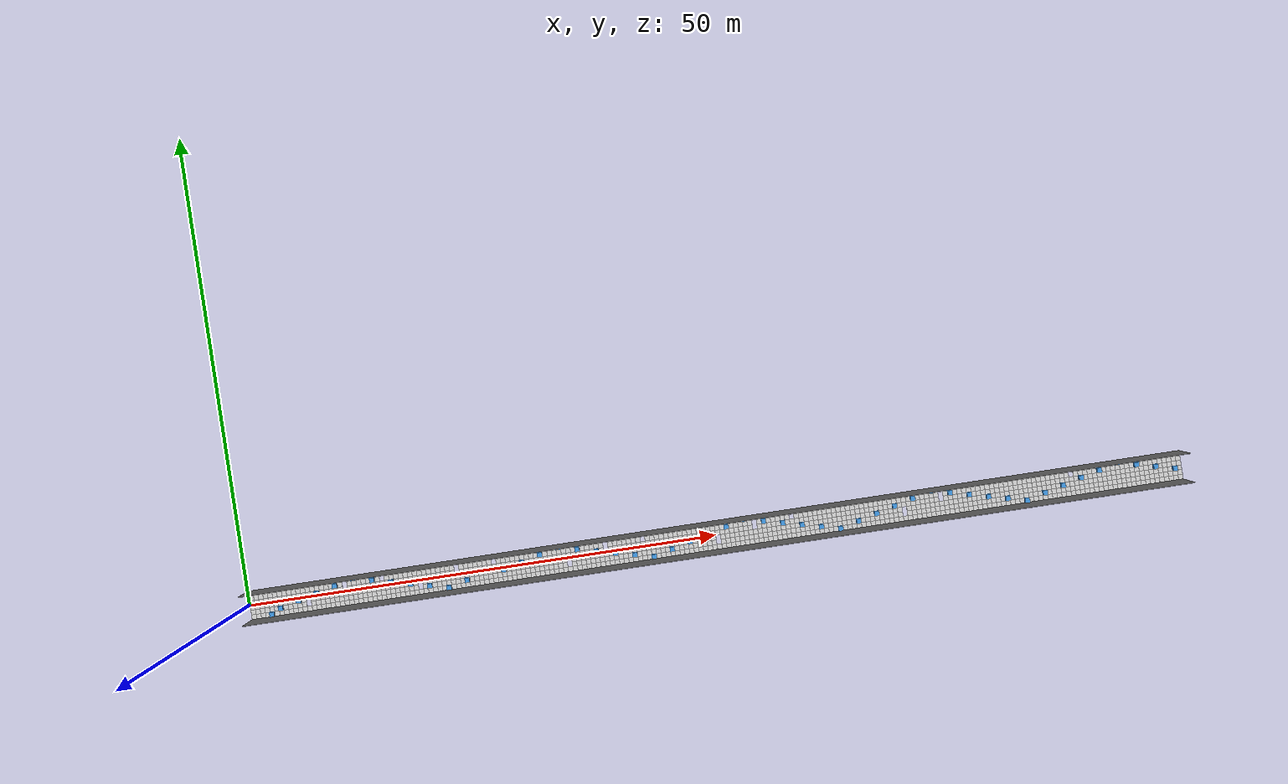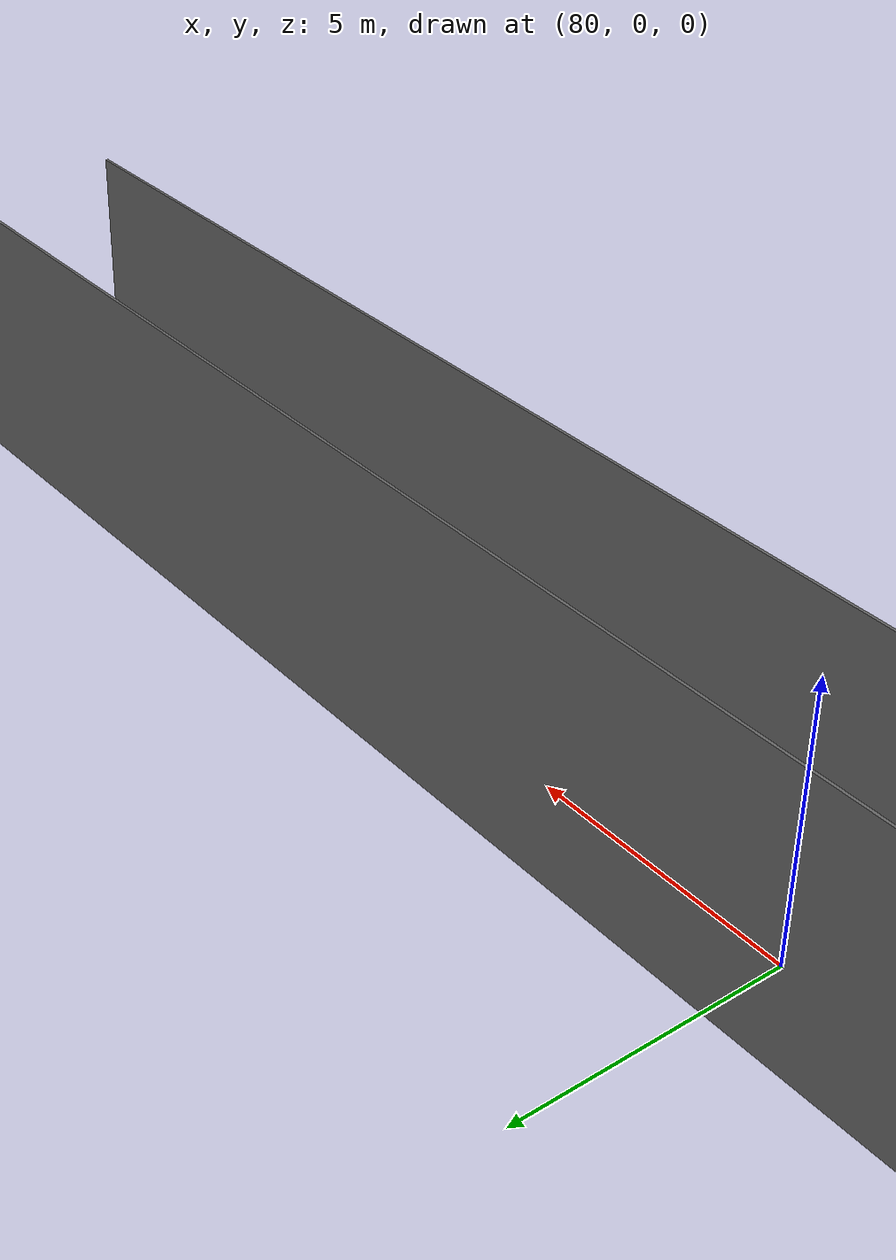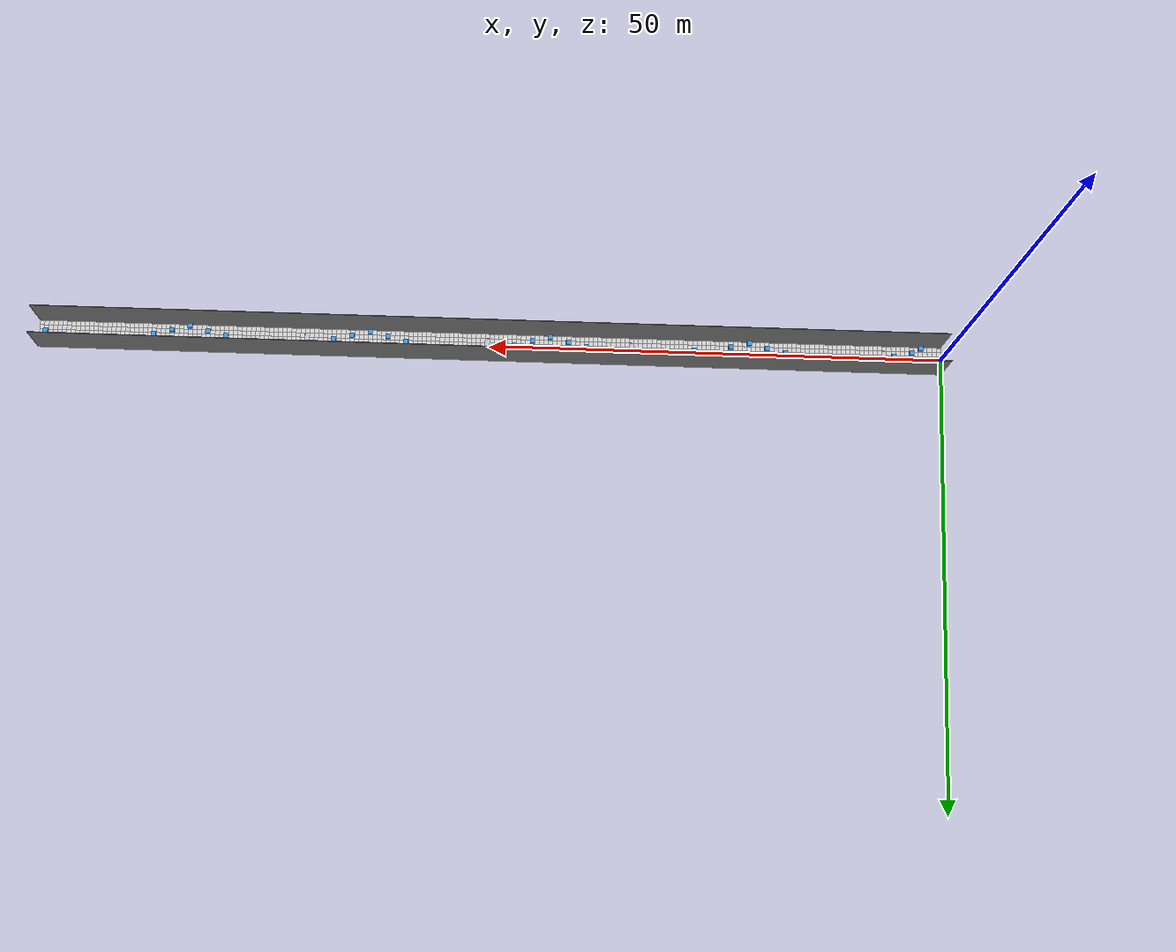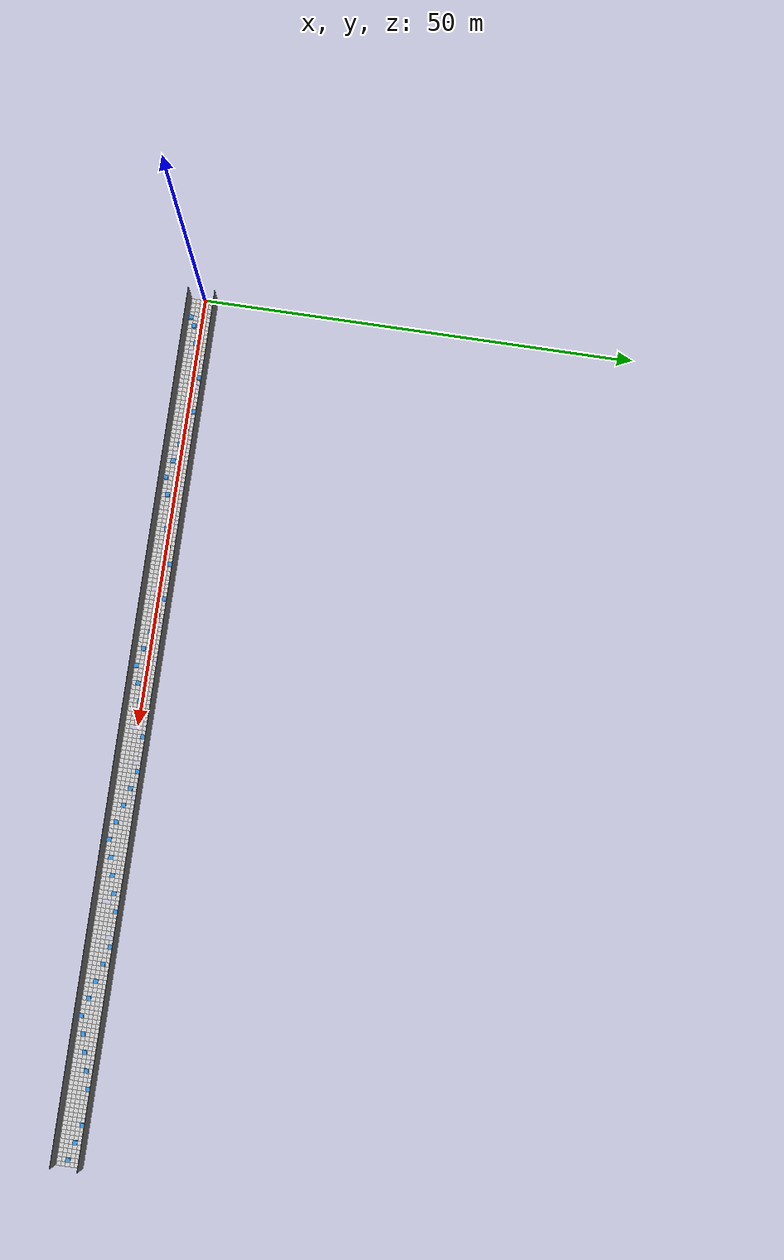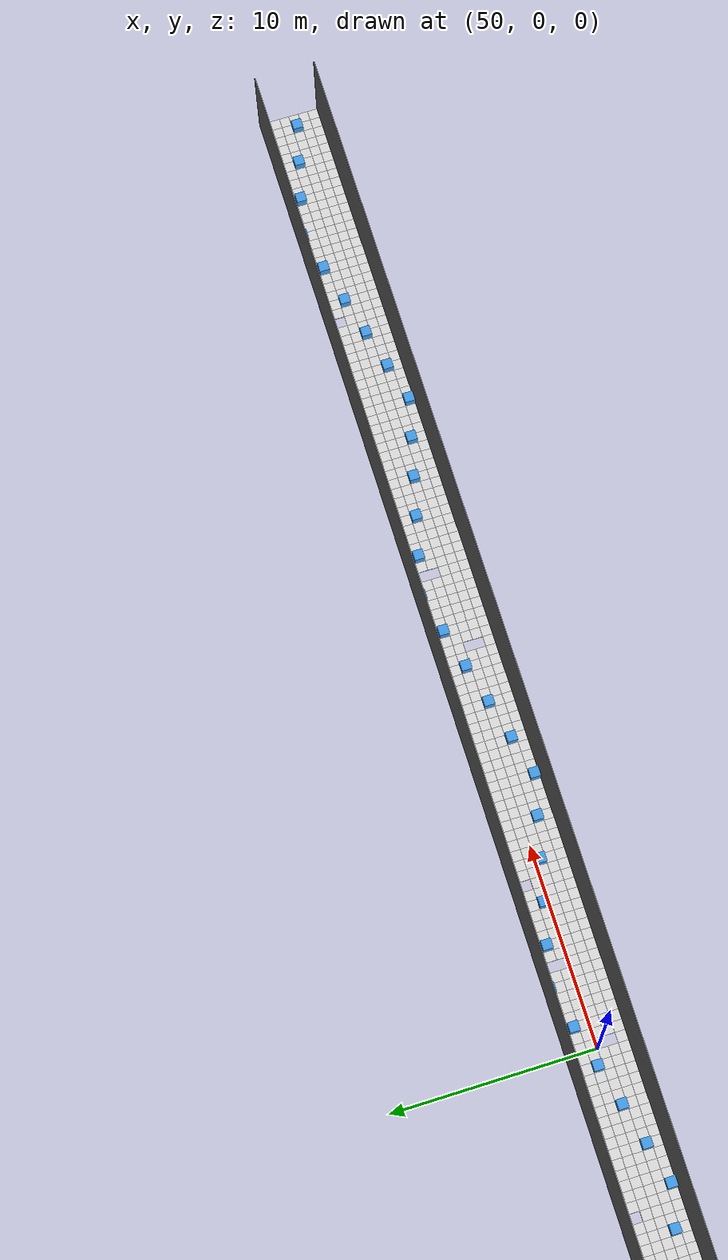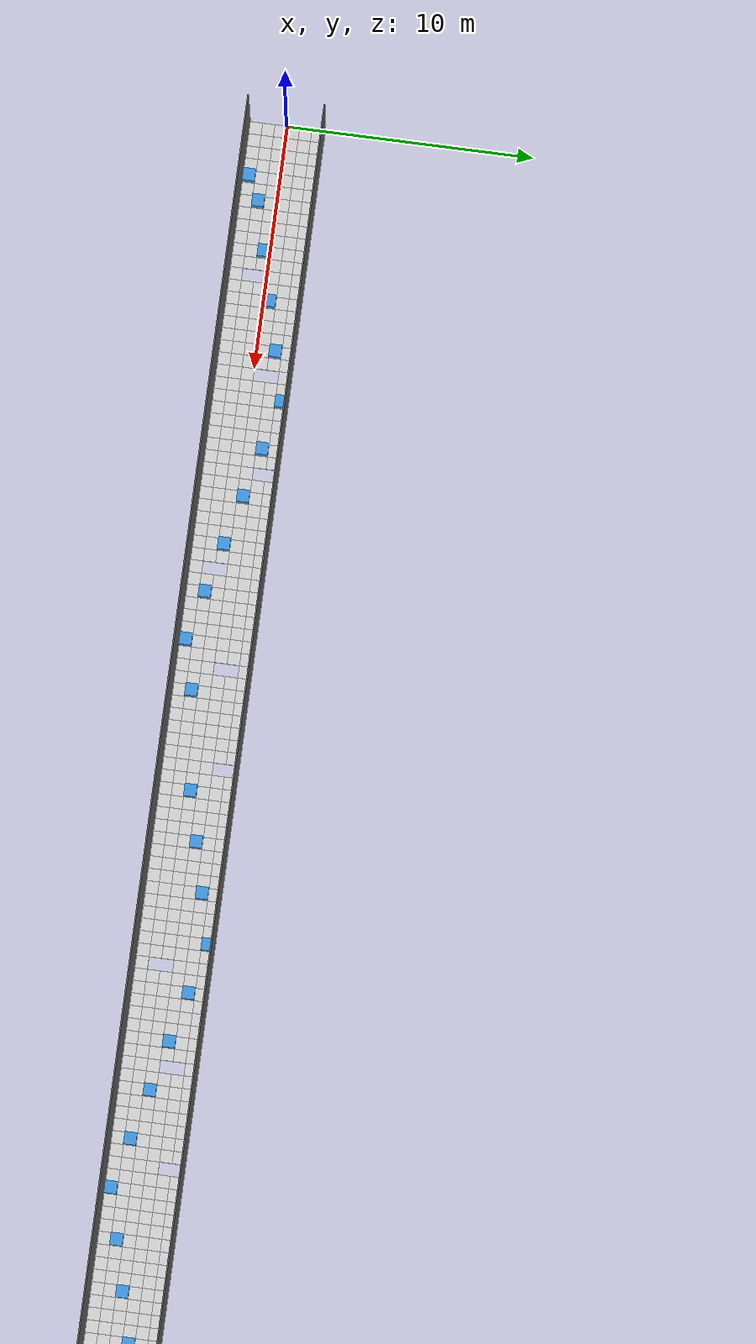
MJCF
<mujoco model="corridor_3x100">
  <compiler angle="degree" autolimits="true"/>
  <option timestep="0.005" gravity="0 0 -9.81"/>
  <size njmax="4000" nconmax="1000"/>
  <asset>
    <material name="mat_floor" rgba="0.85 0.85 0.85 1"/>
    <material name="mat_bump"  rgba="0.25 0.6 0.9 1"/>
    <material name="mat_wall"  rgba="0.4 0.4 0.4 1"/>
    <material name="mat_hole"  rgba="0.8 0.4 0.2 1"/>
  </asset>
  <worldbody>
    <geom name="wall_left" type="box" size="50.000 0.025 2.500" pos="50.000 -1.525 2.500" material="mat_wall"/>
    <geom name="wall_right" type="box" size="50.000 0.025 2.500" pos="50.000 1.525 2.500" material="mat_wall"/>
    <geom type="box" material="mat_floor" name="floor_flat_64" size="0.250 0.250 0.025" pos="0.250 -1.250 0.025"/>
    <geom type="box" material="mat_floor" name="floor_flat_65" size="0.250 0.250 0.025" pos="0.250 -0.750 0.025"/>
    <geom type="box" material="mat_floor" name="floor_flat_66" size="0.250 0.250 0.025" pos="0.250 -0.250 0.025"/>
    <geom type="box" material="mat_floor" name="floor_flat_67" size="0.250 0.250 0.025" pos="0.250 0.250 0.025"/>
    <geom type="box" material="mat_floor" name="floor_flat_68" size="0.250 0.250 0.025" pos="0.250 0.750 0.025"/>
    <geom type="box" material="mat_floor" name="floor_flat_69" size="0.250 0.250 0.025" pos="0.250 1.250 0.025"/>
    <geom type="box" material="mat_floor" name="floor_flat_70" size="0.250 0.250 0.025" pos="0.750 -1.250 0.025"/>
    <geom type="box" material="mat_floor" name="floor_flat_71" size="0.250 0.250 0.025" pos="0.750 -0.750 0.025"/>
    <geom type="box" material="mat_floor" name="floor_flat_72" size="0.250 0.250 0.025" pos="0.750 -0.250 0.025"/>
    <geom type="box" material="mat_floor" name="floor_flat_73" size="0.250 0.250 0.025" pos="0.750 0.250 0.025"/>
    <geom type="box" material="mat_floor" name="floor_flat_74" size="0.250 0.250 0.025" pos="0.750 0.750 0.025"/>
    <geom type="box" material="mat_floor" name="floor_flat_75" size="0.250 0.250 0.025" pos="0.750 1.250 0.025"/>
    <geom type="box" material="mat_floor" name="floor_flat_76" size="0.250 0.250 0.025" pos="1.250 -1.250 0.025"/>
    <geom type="box" material="mat_floor" name="floor_flat_77" size="0.250 0.250 0.025" pos="1.250 -0.750 0.025"/>
    <geom type="box" material="mat_floor" name="floor_flat_78" size="0.250 0.250 0.025" pos="1.250 -0.250 0.025"/>
    <geom type="box" material="mat_floor" name="floor_flat_79" size="0.250 0.250 0.025" pos="1.250 0.250 0.025"/>
    <geom type="box" material="mat_floor" name="floor_flat_80" size="0.250 0.250 0.025" pos="1.250 0.750 0.025"/>
    <geom type="box" material="mat_floor" name="floor_flat_81" size="0.250 0.250 0.025" pos="1.250 1.250 0.025"/>
    <geom type="box" material="mat_floor" name="floor_flat_82" size="0.250 0.250 0.025" pos="1.750 -1.250 0.025"/>
    <geom type="box" material="mat_floor" name="floor_flat_83" size="0.250 0.250 0.025" pos="1.750 -0.750 0.025"/>
    <geom type="box" material="mat_floor" name="floor_flat_84" size="0.250 0.250 0.025" pos="1.750 -0.250 0.025"/>
    <geom type="box" material="mat_floor" name="floor_flat_85" size="0.250 0.250 0.025" pos="1.750 0.250 0.025"/>
    <geom type="box" material="mat_floor" name="floor_flat_86" size="0.250 0.250 0.025" pos="1.750 0.750 0.025"/>
    <geom type="box" material="mat_floor" name="floor_flat_87" size="0.250 0.250 0.025" pos="1.750 1.250 0.025"/>
    <geom type="box" material="mat_floor" name="floor_flat_88" size="0.250 0.250 0.025" pos="2.250 -0.750 0.025"/>
    <geom type="box" material="mat_floor" name="floor_flat_89" size="0.250 0.250 0.025" pos="2.250 -0.250 0.025"/>
    <geom type="box" material="mat_floor" name="floor_flat_90" size="0.250 0.250 0.025" pos="2.250 0.250 0.025"/>
    <geom type="box" material="mat_floor" name="floor_flat_91" size="0.250 0.250 0.025" pos="2.250 0.750 0.025"/>
    <geom type="box" material="mat_floor" name="floor_flat_92" size="0.250 0.250 0.025" pos="2.250 1.250 0.025"/>
    <geom type="box" material="mat_floor" name="floor_flat_93" size="0.250 0.250 0.025" pos="2.750 -1.250 0.025"/>
    <geom type="box" material="mat_floor" name="floor_flat_94" size="0.250 0.250 0.025" pos="2.750 -0.750 0.025"/>
    <geom type="box" material="mat_floor" name="floor_flat_95" size="0.250 0.250 0.025" pos="2.750 -0.250 0.025"/>
    <geom type="box" material="mat_floor" name="floor_flat_96" size="0.250 0.250 0.025" pos="2.750 0.250 0.025"/>
    <geom type="box" material="mat_floor" name="floor_flat_97" size="0.250 0.250 0.025" pos="2.750 0.750 0.025"/>
    <geom type="box" material="mat_floor" name="floor_flat_98" size="0.250 0.250 0.025" pos="2.750 1.250 0.025"/>
    <geom type="box" material="mat_floor" name="floor_flat_99" size="0.250 0.250 0.025" pos="3.250 -1.250 0.025"/>
    <geom type="box" material="mat_floor" name="floor_flat_100" size="0.250 0.250 0.025" pos="3.250 -0.250 0.025"/>
    <geom type="box" material="mat_floor" name="floor_flat_101" size="0.250 0.250 0.025" pos="3.250 0.250 0.025"/>
    <geom type="box" material="mat_floor" name="floor_flat_102" size="0.250 0.250 0.025" pos="3.250 0.750 0.025"/>
    <geom type="box" material="mat_floor" name="floor_flat_103" size="0.250 0.250 0.025" pos="3.250 1.250 0.025"/>
    <geom type="box" material="mat_floor" name="floor_flat_104" size="0.250 0.250 0.025" pos="3.750 -1.250 0.025"/>
    <geom type="box" material="mat_floor" name="floor_flat_105" size="0.250 0.250 0.025" pos="3.750 -0.750 0.025"/>
    <geom type="box" material="mat_floor" name="floor_flat_106" size="0.250 0.250 0.025" pos="3.750 -0.250 0.025"/>
    <geom type="box" material="mat_floor" name="floor_flat_107" size="0.250 0.250 0.025" pos="3.750 0.250 0.025"/>
    <geom type="box" material="mat_floor" name="floor_flat_108" size="0.250 0.250 0.025" pos="3.750 0.750 0.025"/>
    <geom type="box" material="mat_floor" name="floor_flat_109" size="0.250 0.250 0.025" pos="3.750 1.250 0.025"/>
    <geom type="box" material="mat_floor" name="floor_flat_110" size="0.250 0.250 0.025" pos="4.250 -1.250 0.025"/>
    <geom type="box" material="mat_floor" name="floor_flat_111" size="0.250 0.250 0.025" pos="4.250 -0.750 0.025"/>
    <geom type="box" material="mat_floor" name="floor_flat_112" size="0.250 0.250 0.025" pos="4.250 -0.250 0.025"/>
    <geom type="box" material="mat_floor" name="floor_flat_113" size="0.250 0.250 0.025" pos="4.250 0.250 0.025"/>
    <geom type="box" material="mat_floor" name="floor_flat_114" size="0.250 0.250 0.025" pos="4.250 0.750 0.025"/>
    <geom type="box" material="mat_floor" name="floor_flat_115" size="0.250 0.250 0.025" pos="4.250 1.250 0.025"/>
    <geom type="box" material="mat_floor" name="floor_flat_116" size="0.250 0.250 0.025" pos="4.750 -1.250 0.025"/>
    <geom type="box" material="mat_floor" name="floor_flat_117" size="0.250 0.250 0.025" pos="4.750 -0.750 0.025"/>
    <geom type="box" material="mat_floor" name="floor_flat_118" size="0.250 0.250 0.025" pos="4.750 -0.250 0.025"/>
    <geom type="box" material="mat_floor" name="floor_flat_119" size="0.250 0.250 0.025" pos="4.750 0.250 0.025"/>
    <geom type="box" material="mat_floor" name="floor_flat_120" size="0.250 0.250 0.025" pos="4.750 0.750 0.025"/>
    <geom type="box" material="mat_floor" name="floor_flat_121" size="0.250 0.250 0.025" pos="4.750 1.250 0.025"/>
    <geom type="box" material="mat_floor" name="floor_flat_122" size="0.250 0.250 0.025" pos="5.250 -1.250 0.025"/>
    <geom type="box" material="mat_floor" name="floor_flat_123" size="0.250 0.250 0.025" pos="5.250 -0.750 0.025"/>
    <geom type="box" material="mat_floor" name="floor_flat_124" size="0.250 0.250 0.025" pos="5.250 0.250 0.025"/>
    <geom type="box" material="mat_floor" name="floor_flat_125" size="0.250 0.250 0.025" pos="5.250 0.750 0.025"/>
    <geom type="box" material="mat_floor" name="floor_flat_126" size="0.250 0.250 0.025" pos="5.250 1.250 0.025"/>
    <geom type="box" material="mat_floor" name="floor_flat_127" size="0.250 0.250 0.025" pos="5.750 -1.250 0.025"/>
    <geom type="box" material="mat_floor" name="floor_flat_128" size="0.250 0.250 0.025" pos="5.750 -0.750 0.025"/>
    <geom type="box" material="mat_floor" name="floor_flat_129" size="0.250 0.250 0.025" pos="5.750 -0.250 0.025"/>
    <geom type="box" material="mat_floor" name="floor_flat_130" size="0.250 0.250 0.025" pos="5.750 0.250 0.025"/>
    <geom type="box" material="mat_floor" name="floor_flat_131" size="0.250 0.250 0.025" pos="5.750 0.750 0.025"/>
    <geom type="box" material="mat_floor" name="floor_flat_132" size="0.250 0.250 0.025" pos="5.750 1.250 0.025"/>
    <geom type="box" material="mat_floor" name="floor_flat_133" size="0.250 0.250 0.025" pos="6.250 -1.250 0.025"/>
    <geom type="box" material="mat_floor" name="floor_flat_134" size="0.250 0.250 0.025" pos="6.250 0.250 0.025"/>
    <geom type="box" material="mat_floor" name="floor_flat_135" size="0.250 0.250 0.025" pos="6.250 0.750 0.025"/>
    <geom type="box" material="mat_floor" name="floor_flat_136" size="0.250 0.250 0.025" pos="6.250 1.250 0.025"/>
    <geom type="box" material="mat_floor" name="floor_flat_137" size="0.250 0.250 0.025" pos="6.750 -1.250 0.025"/>
    <geom type="box" material="mat_floor" name="floor_flat_138" size="0.250 0.250 0.025" pos="6.750 -0.750 0.025"/>
    <geom type="box" material="mat_floor" name="floor_flat_139" size="0.250 0.250 0.025" pos="6.750 -0.250 0.025"/>
    <geom type="box" material="mat_floor" name="floor_flat_140" size="0.250 0.250 0.025" pos="6.750 0.250 0.025"/>
    <geom type="box" material="mat_floor" name="floor_flat_141" size="0.250 0.250 0.025" pos="6.750 0.750 0.025"/>
    <geom type="box" material="mat_floor" name="floor_flat_142" size="0.250 0.250 0.025" pos="6.750 1.250 0.025"/>
    <geom type="box" material="mat_floor" name="floor_flat_143" size="0.250 0.250 0.025" pos="7.250 -1.250 0.025"/>
    <geom type="box" material="mat_floor" name="floor_flat_144" size="0.250 0.250 0.025" pos="7.250 -0.750 0.025"/>
    <geom type="box" material="mat_floor" name="floor_flat_145" size="0.250 0.250 0.025" pos="7.250 -0.250 0.025"/>
    <geom type="box" material="mat_floor" name="floor_flat_146" size="0.250 0.250 0.025" pos="7.250 0.750 0.025"/>
    <geom type="box" material="mat_floor" name="floor_flat_147" size="0.250 0.250 0.025" pos="7.250 1.250 0.025"/>
    <geom type="box" material="mat_floor" name="floor_flat_148" size="0.250 0.250 0.025" pos="7.750 -1.250 0.025"/>
    <geom type="box" material="mat_floor" name="floor_flat_149" size="0.250 0.250 0.025" pos="7.750 -0.750 0.025"/>
    <geom type="box" material="mat_floor" name="floor_flat_150" size="0.250 0.250 0.025" pos="7.750 -0.250 0.025"/>
    <geom type="box" material="mat_floor" name="floor_flat_151" size="0.250 0.250 0.025" pos="7.750 0.250 0.025"/>
    <geom type="box" material="mat_floor" name="floor_flat_152" size="0.250 0.250 0.025" pos="7.750 0.750 0.025"/>
    <geom type="box" material="mat_floor" name="floor_flat_153" size="0.250 0.250 0.025" pos="7.750 1.250 0.025"/>
    <geom type="box" material="mat_floor" name="floor_flat_154" size="0.250 0.250 0.025" pos="8.250 -1.250 0.025"/>
    <geom type="box" material="mat_floor" name="floor_flat_155" size="0.250 0.250 0.025" pos="8.250 -0.750 0.025"/>
    <geom type="box" material="mat_floor" name="floor_flat_156" size="0.250 0.250 0.025" pos="8.250 -0.250 0.025"/>
    <geom type="box" material="mat_floor" name="floor_flat_157" size="0.250 0.250 0.025" pos="8.250 0.250 0.025"/>
    <geom type="box" material="mat_floor" name="floor_flat_158" size="0.250 0.250 0.025" pos="8.250 0.750 0.025"/>
    <geom type="box" material="mat_floor" name="floor_flat_159" size="0.250 0.250 0.025" pos="8.250 1.250 0.025"/>
    <geom type="box" material="mat_floor" name="floor_flat_160" size="0.250 0.250 0.025" pos="8.750 -1.250 0.025"/>
    <geom type="box" material="mat_floor" name="floor_flat_161" size="0.250 0.250 0.025" pos="8.750 -0.750 0.025"/>
    <geom type="box" material="mat_floor" name="floor_flat_162" size="0.250 0.250 0.025" pos="8.750 -0.250 0.025"/>
    <geom type="box" material="mat_floor" name="floor_flat_163" size="0.250 0.250 0.025" pos="8.750 0.250 0.025"/>
    <geom type="box" material="mat_floor" name="floor_flat_164" size="0.250 0.250 0.025" pos="8.750 0.750 0.025"/>
    <geom type="box" material="mat_floor" name="floor_flat_165" size="0.250 0.250 0.025" pos="8.750 1.250 0.025"/>
    <geom type="box" material="mat_floor" name="floor_flat_166" size="0.250 0.250 0.025" pos="9.250 -1.250 0.025"/>
    <geom type="box" material="mat_floor" name="floor_flat_167" size="0.250 0.250 0.025" pos="9.250 -0.750 0.025"/>
    <geom type="box" material="mat_floor" name="floor_flat_168" size="0.250 0.250 0.025" pos="9.250 -0.250 0.025"/>
    <geom type="box" material="mat_floor" name="floor_flat_169" size="0.250 0.250 0.025" pos="9.250 0.250 0.025"/>
    <geom type="box" material="mat_floor" name="floor_flat_170" size="0.250 0.250 0.025" pos="9.250 1.250 0.025"/>
    <geom type="box" material="mat_floor" name="floor_flat_171" size="0.250 0.250 0.025" pos="9.750 -1.250 0.025"/>
    <geom type="box" material="mat_floor" name="floor_flat_172" size="0.250 0.250 0.025" pos="9.750 -0.750 0.025"/>
    <geom type="box" material="mat_floor" name="floor_flat_173" size="0.250 0.250 0.025" pos="9.750 -0.250 0.025"/>
    <geom type="box" material="mat_floor" name="floor_flat_174" size="0.250 0.250 0.025" pos="9.750 0.250 0.025"/>
    <geom type="box" material="mat_floor" name="floor_flat_175" size="0.250 0.250 0.025" pos="9.750 0.750 0.025"/>
    <geom type="box" material="mat_floor" name="floor_flat_176" size="0.250 0.250 0.025" pos="9.750 1.250 0.025"/>
    <geom type="box" material="mat_floor" name="floor_flat_177" size="0.250 0.250 0.025" pos="10.250 -1.250 0.025"/>
    <geom type="box" material="mat_floor" name="floor_flat_178" size="0.250 0.250 0.025" pos="10.250 -0.750 0.025"/>
    <geom type="box" material="mat_floor" name="floor_flat_179" size="0.250 0.250 0.025" pos="10.250 -0.250 0.025"/>
    <geom type="box" material="mat_floor" name="floor_flat_180" size="0.250 0.250 0.025" pos="10.250 1.250 0.025"/>
    <geom type="box" material="mat_floor" name="floor_flat_181" size="0.250 0.250 0.025" pos="10.750 -1.250 0.025"/>
    <geom type="box" material="mat_floor" name="floor_flat_182" size="0.250 0.250 0.025" pos="10.750 -0.750 0.025"/>
    <geom type="box" material="mat_floor" name="floor_flat_183" size="0.250 0.250 0.025" pos="10.750 -0.250 0.025"/>
    <geom type="box" material="mat_floor" name="floor_flat_184" size="0.250 0.250 0.025" pos="10.750 0.250 0.025"/>
    <geom type="box" material="mat_floor" name="floor_flat_185" size="0.250 0.250 0.025" pos="10.750 0.750 0.025"/>
    <geom type="box" material="mat_floor" name="floor_flat_186" size="0.250 0.250 0.025" pos="10.750 1.250 0.025"/>
    <geom type="box" material="mat_floor" name="floor_flat_187" size="0.250 0.250 0.025" pos="11.250 -1.250 0.025"/>
    <geom type="box" material="mat_floor" name="floor_flat_188" size="0.250 0.250 0.025" pos="11.250 -0.750 0.025"/>
    <geom type="box" material="mat_floor" name="floor_flat_189" size="0.250 0.250 0.025" pos="11.250 -0.250 0.025"/>
    <geom type="box" material="mat_floor" name="floor_flat_190" size="0.250 0.250 0.025" pos="11.250 0.250 0.025"/>
    <geom type="box" material="mat_floor" name="floor_flat_191" size="0.250 0.250 0.025" pos="11.250 0.750 0.025"/>
    <geom type="box" material="mat_floor" name="floor_flat_192" size="0.250 0.250 0.025" pos="11.750 -1.250 0.025"/>
    <geom type="box" material="mat_floor" name="floor_flat_193" size="0.250 0.250 0.025" pos="11.750 -0.750 0.025"/>
    <geom type="box" material="mat_floor" name="floor_flat_194" size="0.250 0.250 0.025" pos="11.750 -0.250 0.025"/>
    <geom type="box" material="mat_floor" name="floor_flat_195" size="0.250 0.250 0.025" pos="11.750 0.250 0.025"/>
    <geom type="box" material="mat_floor" name="floor_flat_196" size="0.250 0.250 0.025" pos="11.750 0.750 0.025"/>
    <geom type="box" material="mat_floor" name="floor_flat_197" size="0.250 0.250 0.025" pos="11.750 1.250 0.025"/>
    <geom type="box" material="mat_floor" name="floor_flat_198" size="0.250 0.250 0.025" pos="12.250 -1.250 0.025"/>
    <geom type="box" material="mat_floor" name="floor_flat_199" size="0.250 0.250 0.025" pos="12.250 -0.750 0.025"/>
    <geom type="box" material="mat_floor" name="floor_flat_200" size="0.250 0.250 0.025" pos="12.250 -0.250 0.025"/>
    <geom type="box" material="mat_floor" name="floor_flat_201" size="0.250 0.250 0.025" pos="12.250 0.250 0.025"/>
    <geom type="box" material="mat_floor" name="floor_flat_202" size="0.250 0.250 0.025" pos="12.250 0.750 0.025"/>
    <geom type="box" material="mat_floor" name="floor_flat_203" size="0.250 0.250 0.025" pos="12.250 1.250 0.025"/>
    <geom type="box" material="mat_floor" name="floor_flat_204" size="0.250 0.250 0.025" pos="12.750 -1.250 0.025"/>
    <geom type="box" material="mat_floor" name="floor_flat_205" size="0.250 0.250 0.025" pos="12.750 -0.750 0.025"/>
    <geom type="box" material="mat_floor" name="floor_flat_206" size="0.250 0.250 0.025" pos="12.750 -0.250 0.025"/>
    <geom type="box" material="mat_floor" name="floor_flat_207" size="0.250 0.250 0.025" pos="12.750 0.250 0.025"/>
    <geom type="box" material="mat_floor" name="floor_flat_208" size="0.250 0.250 0.025" pos="12.750 0.750 0.025"/>
    <geom type="box" material="mat_floor" name="floor_flat_209" size="0.250 0.250 0.025" pos="12.750 1.250 0.025"/>
    <geom type="box" material="mat_floor" name="floor_flat_210" size="0.250 0.250 0.025" pos="13.250 -1.250 0.025"/>
    <geom type="box" material="mat_floor" name="floor_flat_211" size="0.250 0.250 0.025" pos="13.250 -0.750 0.025"/>
    <geom type="box" material="mat_floor" name="floor_flat_212" size="0.250 0.250 0.025" pos="13.250 -0.250 0.025"/>
    <geom type="box" material="mat_floor" name="floor_flat_213" size="0.250 0.250 0.025" pos="13.250 0.250 0.025"/>
    <geom type="box" material="mat_floor" name="floor_flat_214" size="0.250 0.250 0.025" pos="13.250 1.250 0.025"/>
    <geom type="box" material="mat_floor" name="floor_flat_215" size="0.250 0.250 0.025" pos="13.750 -1.250 0.025"/>
    <geom type="box" material="mat_floor" name="floor_flat_216" size="0.250 0.250 0.025" pos="13.750 -0.750 0.025"/>
    <geom type="box" material="mat_floor" name="floor_flat_217" size="0.250 0.250 0.025" pos="13.750 -0.250 0.025"/>
    <geom type="box" material="mat_floor" name="floor_flat_218" size="0.250 0.250 0.025" pos="13.750 0.250 0.025"/>
    <geom type="box" material="mat_floor" name="floor_flat_219" size="0.250 0.250 0.025" pos="13.750 0.750 0.025"/>
    <geom type="box" material="mat_floor" name="floor_flat_220" size="0.250 0.250 0.025" pos="13.750 1.250 0.025"/>
    <geom type="box" material="mat_floor" name="floor_flat_221" size="0.250 0.250 0.025" pos="14.250 -1.250 0.025"/>
    <geom type="box" material="mat_floor" name="floor_flat_222" size="0.250 0.250 0.025" pos="14.250 -0.750 0.025"/>
    <geom type="box" material="mat_floor" name="floor_flat_223" size="0.250 0.250 0.025" pos="14.250 -0.250 0.025"/>
    <geom type="box" material="mat_floor" name="floor_flat_224" size="0.250 0.250 0.025" pos="14.250 0.250 0.025"/>
    <geom type="box" material="mat_floor" name="floor_flat_225" size="0.250 0.250 0.025" pos="14.750 -1.250 0.025"/>
    <geom type="box" material="mat_floor" name="floor_flat_226" size="0.250 0.250 0.025" pos="14.750 -0.750 0.025"/>
    <geom type="box" material="mat_floor" name="floor_flat_227" size="0.250 0.250 0.025" pos="14.750 -0.250 0.025"/>
    <geom type="box" material="mat_floor" name="floor_flat_228" size="0.250 0.250 0.025" pos="14.750 0.250 0.025"/>
    <geom type="box" material="mat_floor" name="floor_flat_229" size="0.250 0.250 0.025" pos="14.750 0.750 0.025"/>
    <geom type="box" material="mat_floor" name="floor_flat_230" size="0.250 0.250 0.025" pos="14.750 1.250 0.025"/>
    <geom type="box" material="mat_floor" name="floor_flat_231" size="0.250 0.250 0.025" pos="15.250 -1.250 0.025"/>
    <geom type="box" material="mat_floor" name="floor_flat_232" size="0.250 0.250 0.025" pos="15.250 -0.750 0.025"/>
    <geom type="box" material="mat_floor" name="floor_flat_233" size="0.250 0.250 0.025" pos="15.250 -0.250 0.025"/>
    <geom type="box" material="mat_floor" name="floor_flat_234" size="0.250 0.250 0.025" pos="15.250 0.750 0.025"/>
    <geom type="box" material="mat_floor" name="floor_flat_235" size="0.250 0.250 0.025" pos="15.250 1.250 0.025"/>
    <geom type="box" material="mat_floor" name="floor_flat_236" size="0.250 0.250 0.025" pos="15.750 -1.250 0.025"/>
    <geom type="box" material="mat_floor" name="floor_flat_237" size="0.250 0.250 0.025" pos="15.750 -0.750 0.025"/>
    <geom type="box" material="mat_floor" name="floor_flat_238" size="0.250 0.250 0.025" pos="15.750 -0.250 0.025"/>
    <geom type="box" material="mat_floor" name="floor_flat_239" size="0.250 0.250 0.025" pos="15.750 0.250 0.025"/>
    <geom type="box" material="mat_floor" name="floor_flat_240" size="0.250 0.250 0.025" pos="15.750 0.750 0.025"/>
    <geom type="box" material="mat_floor" name="floor_flat_241" size="0.250 0.250 0.025" pos="15.750 1.250 0.025"/>
    <geom type="box" material="mat_floor" name="floor_flat_242" size="0.250 0.250 0.025" pos="16.250 -1.250 0.025"/>
    <geom type="box" material="mat_floor" name="floor_flat_243" size="0.250 0.250 0.025" pos="16.250 -0.750 0.025"/>
    <geom type="box" material="mat_floor" name="floor_flat_244" size="0.250 0.250 0.025" pos="16.250 -0.250 0.025"/>
    <geom type="box" material="mat_floor" name="floor_flat_245" size="0.250 0.250 0.025" pos="16.250 0.250 0.025"/>
    <geom type="box" material="mat_floor" name="floor_flat_246" size="0.250 0.250 0.025" pos="16.250 0.750 0.025"/>
    <geom type="box" material="mat_floor" name="floor_flat_247" size="0.250 0.250 0.025" pos="16.250 1.250 0.025"/>
    <geom type="box" material="mat_floor" name="floor_flat_248" size="0.250 0.250 0.025" pos="16.750 -1.250 0.025"/>
    <geom type="box" material="mat_floor" name="floor_flat_249" size="0.250 0.250 0.025" pos="16.750 -0.750 0.025"/>
    <geom type="box" material="mat_floor" name="floor_flat_250" size="0.250 0.250 0.025" pos="16.750 -0.250 0.025"/>
    <geom type="box" material="mat_floor" name="floor_flat_251" size="0.250 0.250 0.025" pos="16.750 0.250 0.025"/>
    <geom type="box" material="mat_floor" name="floor_flat_252" size="0.250 0.250 0.025" pos="16.750 0.750 0.025"/>
    <geom type="box" material="mat_floor" name="floor_flat_253" size="0.250 0.250 0.025" pos="16.750 1.250 0.025"/>
    <geom type="box" material="mat_floor" name="floor_flat_254" size="0.250 0.250 0.025" pos="17.250 -1.250 0.025"/>
    <geom type="box" material="mat_floor" name="floor_flat_255" size="0.250 0.250 0.025" pos="17.250 -0.750 0.025"/>
    <geom type="box" material="mat_floor" name="floor_flat_256" size="0.250 0.250 0.025" pos="17.250 0.250 0.025"/>
    <geom type="box" material="mat_floor" name="floor_flat_257" size="0.250 0.250 0.025" pos="17.250 0.750 0.025"/>
    <geom type="box" material="mat_floor" name="floor_flat_258" size="0.250 0.250 0.025" pos="17.250 1.250 0.025"/>
    <geom type="box" material="mat_floor" name="floor_flat_259" size="0.250 0.250 0.025" pos="17.750 -1.250 0.025"/>
    <geom type="box" material="mat_floor" name="floor_flat_260" size="0.250 0.250 0.025" pos="17.750 -0.750 0.025"/>
    <geom type="box" material="mat_floor" name="floor_flat_261" size="0.250 0.250 0.025" pos="17.750 -0.250 0.025"/>
    <geom type="box" material="mat_floor" name="floor_flat_262" size="0.250 0.250 0.025" pos="17.750 0.250 0.025"/>
    <geom type="box" material="mat_floor" name="floor_flat_263" size="0.250 0.250 0.025" pos="17.750 0.750 0.025"/>
    <geom type="box" material="mat_floor" name="floor_flat_264" size="0.250 0.250 0.025" pos="17.750 1.250 0.025"/>
    <geom type="box" material="mat_floor" name="floor_flat_265" size="0.250 0.250 0.025" pos="18.250 -1.250 0.025"/>
    <geom type="box" material="mat_floor" name="floor_flat_266" size="0.250 0.250 0.025" pos="18.250 0.250 0.025"/>
    <geom type="box" material="mat_floor" name="floor_flat_267" size="0.250 0.250 0.025" pos="18.250 0.750 0.025"/>
    <geom type="box" material="mat_floor" name="floor_flat_268" size="0.250 0.250 0.025" pos="18.250 1.250 0.025"/>
    <geom type="box" material="mat_floor" name="floor_flat_269" size="0.250 0.250 0.025" pos="18.750 -1.250 0.025"/>
    <geom type="box" material="mat_floor" name="floor_flat_270" size="0.250 0.250 0.025" pos="18.750 -0.750 0.025"/>
    <geom type="box" material="mat_floor" name="floor_flat_271" size="0.250 0.250 0.025" pos="18.750 -0.250 0.025"/>
    <geom type="box" material="mat_floor" name="floor_flat_272" size="0.250 0.250 0.025" pos="18.750 0.250 0.025"/>
    <geom type="box" material="mat_floor" name="floor_flat_273" size="0.250 0.250 0.025" pos="18.750 0.750 0.025"/>
    <geom type="box" material="mat_floor" name="floor_flat_274" size="0.250 0.250 0.025" pos="18.750 1.250 0.025"/>
    <geom type="box" material="mat_floor" name="floor_flat_275" size="0.250 0.250 0.025" pos="19.250 -1.250 0.025"/>
    <geom type="box" material="mat_floor" name="floor_flat_276" size="0.250 0.250 0.025" pos="19.250 -0.250 0.025"/>
    <geom type="box" material="mat_floor" name="floor_flat_277" size="0.250 0.250 0.025" pos="19.250 0.250 0.025"/>
    <geom type="box" material="mat_floor" name="floor_flat_278" size="0.250 0.250 0.025" pos="19.250 0.750 0.025"/>
    <geom type="box" material="mat_floor" name="floor_flat_279" size="0.250 0.250 0.025" pos="19.250 1.250 0.025"/>
    <geom type="box" material="mat_floor" name="floor_flat_280" size="0.250 0.250 0.025" pos="19.750 -1.250 0.025"/>
    <geom type="box" material="mat_floor" name="floor_flat_281" size="0.250 0.250 0.025" pos="19.750 -0.750 0.025"/>
    <geom type="box" material="mat_floor" name="floor_flat_282" size="0.250 0.250 0.025" pos="19.750 -0.250 0.025"/>
    <geom type="box" material="mat_floor" name="floor_flat_283" size="0.250 0.250 0.025" pos="19.750 0.250 0.025"/>
    <geom type="box" material="mat_floor" name="floor_flat_284" size="0.250 0.250 0.025" pos="19.750 0.750 0.025"/>
    <geom type="box" material="mat_floor" name="floor_flat_285" size="0.250 0.250 0.025" pos="19.750 1.250 0.025"/>
    <geom type="box" material="mat_floor" name="floor_flat_286" size="0.250 0.250 0.025" pos="20.250 -1.250 0.025"/>
    <geom type="box" material="mat_floor" name="floor_flat_287" size="0.250 0.250 0.025" pos="20.250 -0.750 0.025"/>
    <geom type="box" material="mat_floor" name="floor_flat_288" size="0.250 0.250 0.025" pos="20.250 -0.250 0.025"/>
    <geom type="box" material="mat_floor" name="floor_flat_289" size="0.250 0.250 0.025" pos="20.250 0.250 0.025"/>
    <geom type="box" material="mat_floor" name="floor_flat_290" size="0.250 0.250 0.025" pos="20.250 0.750 0.025"/>
    <geom type="box" material="mat_floor" name="floor_flat_291" size="0.250 0.250 0.025" pos="20.250 1.250 0.025"/>
    <geom type="box" material="mat_floor" name="floor_flat_292" size="0.250 0.250 0.025" pos="20.750 -1.250 0.025"/>
    <geom type="box" material="mat_floor" name="floor_flat_293" size="0.250 0.250 0.025" pos="20.750 -0.750 0.025"/>
    <geom type="box" material="mat_floor" name="floor_flat_294" size="0.250 0.250 0.025" pos="20.750 -0.250 0.025"/>
    <geom type="box" material="mat_floor" name="floor_flat_295" size="0.250 0.250 0.025" pos="20.750 0.250 0.025"/>
    <geom type="box" material="mat_floor" name="floor_flat_296" size="0.250 0.250 0.025" pos="20.750 0.750 0.025"/>
    <geom type="box" material="mat_floor" name="floor_flat_297" size="0.250 0.250 0.025" pos="20.750 1.250 0.025"/>
    <geom type="box" material="mat_floor" name="floor_flat_298" size="0.250 0.250 0.025" pos="21.250 -0.750 0.025"/>
    <geom type="box" material="mat_floor" name="floor_flat_299" size="0.250 0.250 0.025" pos="21.250 -0.250 0.025"/>
    <geom type="box" material="mat_floor" name="floor_flat_300" size="0.250 0.250 0.025" pos="21.250 0.250 0.025"/>
    <geom type="box" material="mat_floor" name="floor_flat_301" size="0.250 0.250 0.025" pos="21.250 0.750 0.025"/>
    <geom type="box" material="mat_floor" name="floor_flat_302" size="0.250 0.250 0.025" pos="21.250 1.250 0.025"/>
    <geom type="box" material="mat_floor" name="floor_flat_303" size="0.250 0.250 0.025" pos="21.750 -1.250 0.025"/>
    <geom type="box" material="mat_floor" name="floor_flat_304" size="0.250 0.250 0.025" pos="21.750 -0.750 0.025"/>
    <geom type="box" material="mat_floor" name="floor_flat_305" size="0.250 0.250 0.025" pos="21.750 -0.250 0.025"/>
    <geom type="box" material="mat_floor" name="floor_flat_306" size="0.250 0.250 0.025" pos="21.750 0.250 0.025"/>
    <geom type="box" material="mat_floor" name="floor_flat_307" size="0.250 0.250 0.025" pos="21.750 0.750 0.025"/>
    <geom type="box" material="mat_floor" name="floor_flat_308" size="0.250 0.250 0.025" pos="21.750 1.250 0.025"/>
    <geom type="box" material="mat_floor" name="floor_flat_309" size="0.250 0.250 0.025" pos="22.250 -1.250 0.025"/>
    <geom type="box" material="mat_floor" name="floor_flat_310" size="0.250 0.250 0.025" pos="22.250 -0.750 0.025"/>
    <geom type="box" material="mat_floor" name="floor_flat_311" size="0.250 0.250 0.025" pos="22.250 -0.250 0.025"/>
    <geom type="box" material="mat_floor" name="floor_flat_312" size="0.250 0.250 0.025" pos="22.250 1.250 0.025"/>
    <geom type="box" material="mat_floor" name="floor_flat_313" size="0.250 0.250 0.025" pos="22.750 -1.250 0.025"/>
    <geom type="box" material="mat_floor" name="floor_flat_314" size="0.250 0.250 0.025" pos="22.750 -0.750 0.025"/>
    <geom type="box" material="mat_floor" name="floor_flat_315" size="0.250 0.250 0.025" pos="22.750 -0.250 0.025"/>
    <geom type="box" material="mat_floor" name="floor_flat_316" size="0.250 0.250 0.025" pos="22.750 0.250 0.025"/>
    <geom type="box" material="mat_floor" name="floor_flat_317" size="0.250 0.250 0.025" pos="22.750 0.750 0.025"/>
    <geom type="box" material="mat_floor" name="floor_flat_318" size="0.250 0.250 0.025" pos="22.750 1.250 0.025"/>
    <geom type="box" material="mat_floor" name="floor_flat_319" size="0.250 0.250 0.025" pos="23.250 -1.250 0.025"/>
    <geom type="box" material="mat_floor" name="floor_flat_320" size="0.250 0.250 0.025" pos="23.250 -0.250 0.025"/>
    <geom type="box" material="mat_floor" name="floor_flat_321" size="0.250 0.250 0.025" pos="23.250 0.250 0.025"/>
    <geom type="box" material="mat_floor" name="floor_flat_322" size="0.250 0.250 0.025" pos="23.250 0.750 0.025"/>
    <geom type="box" material="mat_floor" name="floor_flat_323" size="0.250 0.250 0.025" pos="23.250 1.250 0.025"/>
    <geom type="box" material="mat_floor" name="floor_flat_324" size="0.250 0.250 0.025" pos="23.750 -1.250 0.025"/>
    <geom type="box" material="mat_floor" name="floor_flat_325" size="0.250 0.250 0.025" pos="23.750 -0.750 0.025"/>
    <geom type="box" material="mat_floor" name="floor_flat_326" size="0.250 0.250 0.025" pos="23.750 -0.250 0.025"/>
    <geom type="box" material="mat_floor" name="floor_flat_327" size="0.250 0.250 0.025" pos="23.750 0.250 0.025"/>
    <geom type="box" material="mat_floor" name="floor_flat_328" size="0.250 0.250 0.025" pos="23.750 0.750 0.025"/>
    <geom type="box" material="mat_floor" name="floor_flat_329" size="0.250 0.250 0.025" pos="23.750 1.250 0.025"/>
    <geom type="box" material="mat_floor" name="floor_flat_330" size="0.250 0.250 0.025" pos="24.250 -1.250 0.025"/>
    <geom type="box" material="mat_floor" name="floor_flat_331" size="0.250 0.250 0.025" pos="24.250 -0.750 0.025"/>
    <geom type="box" material="mat_floor" name="floor_flat_332" size="0.250 0.250 0.025" pos="24.250 -0.250 0.025"/>
    <geom type="box" material="mat_floor" name="floor_flat_333" size="0.250 0.250 0.025" pos="24.250 0.250 0.025"/>
    <geom type="box" material="mat_floor" name="floor_flat_334" size="0.250 0.250 0.025" pos="24.250 0.750 0.025"/>
    <geom type="box" material="mat_floor" name="floor_flat_335" size="0.250 0.250 0.025" pos="24.250 1.250 0.025"/>
    <geom type="box" material="mat_floor" name="floor_flat_336" size="0.250 0.250 0.025" pos="24.750 -1.250 0.025"/>
    <geom type="box" material="mat_floor" name="floor_flat_337" size="0.250 0.250 0.025" pos="24.750 -0.750 0.025"/>
    <geom type="box" material="mat_floor" name="floor_flat_338" size="0.250 0.250 0.025" pos="24.750 -0.250 0.025"/>
    <geom type="box" material="mat_floor" name="floor_flat_339" size="0.250 0.250 0.025" pos="24.750 0.250 0.025"/>
    <geom type="box" material="mat_floor" name="floor_flat_340" size="0.250 0.250 0.025" pos="24.750 0.750 0.025"/>
    <geom type="box" material="mat_floor" name="floor_flat_341" size="0.250 0.250 0.025" pos="24.750 1.250 0.025"/>
    <geom type="box" material="mat_floor" name="floor_flat_342" size="0.250 0.250 0.025" pos="25.250 -1.250 0.025"/>
    <geom type="box" material="mat_floor" name="floor_flat_343" size="0.250 0.250 0.025" pos="25.250 -0.750 0.025"/>
    <geom type="box" material="mat_floor" name="floor_flat_344" size="0.250 0.250 0.025" pos="25.250 -0.250 0.025"/>
    <geom type="box" material="mat_floor" name="floor_flat_345" size="0.250 0.250 0.025" pos="25.250 0.250 0.025"/>
    <geom type="box" material="mat_floor" name="floor_flat_346" size="0.250 0.250 0.025" pos="25.250 0.750 0.025"/>
    <geom type="box" material="mat_floor" name="floor_flat_347" size="0.250 0.250 0.025" pos="25.250 1.250 0.025"/>
    <geom type="box" material="mat_floor" name="floor_flat_348" size="0.250 0.250 0.025" pos="25.750 -1.250 0.025"/>
    <geom type="box" material="mat_floor" name="floor_flat_349" size="0.250 0.250 0.025" pos="25.750 -0.750 0.025"/>
    <geom type="box" material="mat_floor" name="floor_flat_350" size="0.250 0.250 0.025" pos="25.750 -0.250 0.025"/>
    <geom type="box" material="mat_floor" name="floor_flat_351" size="0.250 0.250 0.025" pos="25.750 0.250 0.025"/>
    <geom type="box" material="mat_floor" name="floor_flat_352" size="0.250 0.250 0.025" pos="25.750 0.750 0.025"/>
    <geom type="box" material="mat_floor" name="floor_flat_353" size="0.250 0.250 0.025" pos="25.750 1.250 0.025"/>
    <geom type="box" material="mat_floor" name="floor_flat_354" size="0.250 0.250 0.025" pos="26.250 -1.250 0.025"/>
    <geom type="box" material="mat_floor" name="floor_flat_355" size="0.250 0.250 0.025" pos="26.250 -0.750 0.025"/>
    <geom type="box" material="mat_floor" name="floor_flat_356" size="0.250 0.250 0.025" pos="26.250 -0.250 0.025"/>
    <geom type="box" material="mat_floor" name="floor_flat_357" size="0.250 0.250 0.025" pos="26.250 0.250 0.025"/>
    <geom type="box" material="mat_floor" name="floor_flat_358" size="0.250 0.250 0.025" pos="26.750 -1.250 0.025"/>
    <geom type="box" material="mat_floor" name="floor_flat_359" size="0.250 0.250 0.025" pos="26.750 -0.750 0.025"/>
    <geom type="box" material="mat_floor" name="floor_flat_360" size="0.250 0.250 0.025" pos="26.750 -0.250 0.025"/>
    <geom type="box" material="mat_floor" name="floor_flat_361" size="0.250 0.250 0.025" pos="26.750 0.250 0.025"/>
    <geom type="box" material="mat_floor" name="floor_flat_362" size="0.250 0.250 0.025" pos="26.750 0.750 0.025"/>
    <geom type="box" material="mat_floor" name="floor_flat_363" size="0.250 0.250 0.025" pos="26.750 1.250 0.025"/>
    <geom type="box" material="mat_floor" name="floor_flat_364" size="0.250 0.250 0.025" pos="27.250 -1.250 0.025"/>
    <geom type="box" material="mat_floor" name="floor_flat_365" size="0.250 0.250 0.025" pos="27.250 -0.750 0.025"/>
    <geom type="box" material="mat_floor" name="floor_flat_366" size="0.250 0.250 0.025" pos="27.250 0.250 0.025"/>
    <geom type="box" material="mat_floor" name="floor_flat_367" size="0.250 0.250 0.025" pos="27.250 0.750 0.025"/>
    <geom type="box" material="mat_floor" name="floor_flat_368" size="0.250 0.250 0.025" pos="27.250 1.250 0.025"/>
    <geom type="box" material="mat_floor" name="floor_flat_369" size="0.250 0.250 0.025" pos="27.750 -1.250 0.025"/>
    <geom type="box" material="mat_floor" name="floor_flat_370" size="0.250 0.250 0.025" pos="27.750 -0.750 0.025"/>
    <geom type="box" material="mat_floor" name="floor_flat_371" size="0.250 0.250 0.025" pos="27.750 -0.250 0.025"/>
    <geom type="box" material="mat_floor" name="floor_flat_372" size="0.250 0.250 0.025" pos="27.750 0.250 0.025"/>
    <geom type="box" material="mat_floor" name="floor_flat_373" size="0.250 0.250 0.025" pos="27.750 0.750 0.025"/>
    <geom type="box" material="mat_floor" name="floor_flat_374" size="0.250 0.250 0.025" pos="27.750 1.250 0.025"/>
    <geom type="box" material="mat_floor" name="floor_flat_375" size="0.250 0.250 0.025" pos="28.250 -1.250 0.025"/>
    <geom type="box" material="mat_floor" name="floor_flat_376" size="0.250 0.250 0.025" pos="28.250 -0.750 0.025"/>
    <geom type="box" material="mat_floor" name="floor_flat_377" size="0.250 0.250 0.025" pos="28.250 -0.250 0.025"/>
    <geom type="box" material="mat_floor" name="floor_flat_378" size="0.250 0.250 0.025" pos="28.250 0.250 0.025"/>
    <geom type="box" material="mat_floor" name="floor_flat_379" size="0.250 0.250 0.025" pos="28.250 0.750 0.025"/>
    <geom type="box" material="mat_floor" name="floor_flat_380" size="0.250 0.250 0.025" pos="28.250 1.250 0.025"/>
    <geom type="box" material="mat_floor" name="floor_flat_381" size="0.250 0.250 0.025" pos="28.750 -1.250 0.025"/>
    <geom type="box" material="mat_floor" name="floor_flat_382" size="0.250 0.250 0.025" pos="28.750 -0.750 0.025"/>
    <geom type="box" material="mat_floor" name="floor_flat_383" size="0.250 0.250 0.025" pos="28.750 -0.250 0.025"/>
    <geom type="box" material="mat_floor" name="floor_flat_384" size="0.250 0.250 0.025" pos="28.750 0.250 0.025"/>
    <geom type="box" material="mat_floor" name="floor_flat_385" size="0.250 0.250 0.025" pos="28.750 0.750 0.025"/>
    <geom type="box" material="mat_floor" name="floor_flat_386" size="0.250 0.250 0.025" pos="28.750 1.250 0.025"/>
    <geom type="box" material="mat_floor" name="floor_flat_387" size="0.250 0.250 0.025" pos="29.250 -1.250 0.025"/>
    <geom type="box" material="mat_floor" name="floor_flat_388" size="0.250 0.250 0.025" pos="29.250 -0.750 0.025"/>
    <geom type="box" material="mat_floor" name="floor_flat_389" size="0.250 0.250 0.025" pos="29.250 -0.250 0.025"/>
    <geom type="box" material="mat_floor" name="floor_flat_390" size="0.250 0.250 0.025" pos="29.250 0.750 0.025"/>
    <geom type="box" material="mat_floor" name="floor_flat_391" size="0.250 0.250 0.025" pos="29.250 1.250 0.025"/>
    <geom type="box" material="mat_floor" name="floor_flat_392" size="0.250 0.250 0.025" pos="29.750 -1.250 0.025"/>
    <geom type="box" material="mat_floor" name="floor_flat_393" size="0.250 0.250 0.025" pos="29.750 -0.750 0.025"/>
    <geom type="box" material="mat_floor" name="floor_flat_394" size="0.250 0.250 0.025" pos="29.750 -0.250 0.025"/>
    <geom type="box" material="mat_floor" name="floor_flat_395" size="0.250 0.250 0.025" pos="29.750 0.250 0.025"/>
    <geom type="box" material="mat_floor" name="floor_flat_396" size="0.250 0.250 0.025" pos="29.750 0.750 0.025"/>
    <geom type="box" material="mat_floor" name="floor_flat_397" size="0.250 0.250 0.025" pos="29.750 1.250 0.025"/>
    <geom type="box" material="mat_floor" name="floor_flat_398" size="0.250 0.250 0.025" pos="30.250 -1.250 0.025"/>
    <geom type="box" material="mat_floor" name="floor_flat_399" size="0.250 0.250 0.025" pos="30.250 -0.750 0.025"/>
    <geom type="box" material="mat_floor" name="floor_flat_400" size="0.250 0.250 0.025" pos="30.250 -0.250 0.025"/>
    <geom type="box" material="mat_floor" name="floor_flat_401" size="0.250 0.250 0.025" pos="30.250 0.250 0.025"/>
    <geom type="box" material="mat_floor" name="floor_flat_402" size="0.250 0.250 0.025" pos="30.250 0.750 0.025"/>
    <geom type="box" material="mat_floor" name="floor_flat_403" size="0.250 0.250 0.025" pos="30.250 1.250 0.025"/>
    <geom type="box" material="mat_floor" name="floor_flat_404" size="0.250 0.250 0.025" pos="30.750 -1.250 0.025"/>
    <geom type="box" material="mat_floor" name="floor_flat_405" size="0.250 0.250 0.025" pos="30.750 -0.750 0.025"/>
    <geom type="box" material="mat_floor" name="floor_flat_406" size="0.250 0.250 0.025" pos="30.750 -0.250 0.025"/>
    <geom type="box" material="mat_floor" name="floor_flat_407" size="0.250 0.250 0.025" pos="30.750 0.250 0.025"/>
    <geom type="box" material="mat_floor" name="floor_flat_408" size="0.250 0.250 0.025" pos="30.750 0.750 0.025"/>
    <geom type="box" material="mat_floor" name="floor_flat_409" size="0.250 0.250 0.025" pos="30.750 1.250 0.025"/>
    <geom type="box" material="mat_floor" name="floor_flat_410" size="0.250 0.250 0.025" pos="31.250 -1.250 0.025"/>
    <geom type="box" material="mat_floor" name="floor_flat_411" size="0.250 0.250 0.025" pos="31.250 -0.750 0.025"/>
    <geom type="box" material="mat_floor" name="floor_flat_412" size="0.250 0.250 0.025" pos="31.250 -0.250 0.025"/>
    <geom type="box" material="mat_floor" name="floor_flat_413" size="0.250 0.250 0.025" pos="31.250 0.250 0.025"/>
    <geom type="box" material="mat_floor" name="floor_flat_414" size="0.250 0.250 0.025" pos="31.250 1.250 0.025"/>
    <geom type="box" material="mat_floor" name="floor_flat_415" size="0.250 0.250 0.025" pos="31.750 -1.250 0.025"/>
    <geom type="box" material="mat_floor" name="floor_flat_416" size="0.250 0.250 0.025" pos="31.750 -0.750 0.025"/>
    <geom type="box" material="mat_floor" name="floor_flat_417" size="0.250 0.250 0.025" pos="31.750 -0.250 0.025"/>
    <geom type="box" material="mat_floor" name="floor_flat_418" size="0.250 0.250 0.025" pos="31.750 0.250 0.025"/>
    <geom type="box" material="mat_floor" name="floor_flat_419" size="0.250 0.250 0.025" pos="31.750 0.750 0.025"/>
    <geom type="box" material="mat_floor" name="floor_flat_420" size="0.250 0.250 0.025" pos="31.750 1.250 0.025"/>
    <geom type="box" material="mat_floor" name="floor_flat_421" size="0.250 0.250 0.025" pos="32.250 -1.250 0.025"/>
    <geom type="box" material="mat_floor" name="floor_flat_422" size="0.250 0.250 0.025" pos="32.250 -0.750 0.025"/>
    <geom type="box" material="mat_floor" name="floor_flat_423" size="0.250 0.250 0.025" pos="32.250 -0.250 0.025"/>
    <geom type="box" material="mat_floor" name="floor_flat_424" size="0.250 0.250 0.025" pos="32.250 0.250 0.025"/>
    <geom type="box" material="mat_floor" name="floor_flat_425" size="0.250 0.250 0.025" pos="32.250 0.750 0.025"/>
    <geom type="box" material="mat_floor" name="floor_flat_426" size="0.250 0.250 0.025" pos="32.250 1.250 0.025"/>
    <geom type="box" material="mat_floor" name="floor_flat_427" size="0.250 0.250 0.025" pos="32.750 -1.250 0.025"/>
    <geom type="box" material="mat_floor" name="floor_flat_428" size="0.250 0.250 0.025" pos="32.750 -0.750 0.025"/>
    <geom type="box" material="mat_floor" name="floor_flat_429" size="0.250 0.250 0.025" pos="32.750 -0.250 0.025"/>
    <geom type="box" material="mat_floor" name="floor_flat_430" size="0.250 0.250 0.025" pos="32.750 0.250 0.025"/>
    <geom type="box" material="mat_floor" name="floor_flat_431" size="0.250 0.250 0.025" pos="32.750 0.750 0.025"/>
    <geom type="box" material="mat_floor" name="floor_flat_432" size="0.250 0.250 0.025" pos="32.750 1.250 0.025"/>
    <geom type="box" material="mat_floor" name="floor_flat_433" size="0.250 0.250 0.025" pos="33.250 -1.250 0.025"/>
    <geom type="box" material="mat_floor" name="floor_flat_434" size="0.250 0.250 0.025" pos="33.250 -0.750 0.025"/>
    <geom type="box" material="mat_floor" name="floor_flat_435" size="0.250 0.250 0.025" pos="33.250 -0.250 0.025"/>
    <geom type="box" material="mat_floor" name="floor_flat_436" size="0.250 0.250 0.025" pos="33.250 0.250 0.025"/>
    <geom type="box" material="mat_floor" name="floor_flat_437" size="0.250 0.250 0.025" pos="33.250 0.750 0.025"/>
    <geom type="box" material="mat_floor" name="floor_flat_438" size="0.250 0.250 0.025" pos="33.750 -1.250 0.025"/>
    <geom type="box" material="mat_floor" name="floor_flat_439" size="0.250 0.250 0.025" pos="33.750 -0.750 0.025"/>
    <geom type="box" material="mat_floor" name="floor_flat_440" size="0.250 0.250 0.025" pos="33.750 -0.250 0.025"/>
    <geom type="box" material="mat_floor" name="floor_flat_441" size="0.250 0.250 0.025" pos="33.750 0.250 0.025"/>
    <geom type="box" material="mat_floor" name="floor_flat_442" size="0.250 0.250 0.025" pos="33.750 0.750 0.025"/>
    <geom type="box" material="mat_floor" name="floor_flat_443" size="0.250 0.250 0.025" pos="33.750 1.250 0.025"/>
    <geom type="box" material="mat_floor" name="floor_flat_444" size="0.250 0.250 0.025" pos="34.250 -1.250 0.025"/>
    <geom type="box" material="mat_floor" name="floor_flat_445" size="0.250 0.250 0.025" pos="34.250 0.250 0.025"/>
    <geom type="box" material="mat_floor" name="floor_flat_446" size="0.250 0.250 0.025" pos="34.250 0.750 0.025"/>
    <geom type="box" material="mat_floor" name="floor_flat_447" size="0.250 0.250 0.025" pos="34.250 1.250 0.025"/>
    <geom type="box" material="mat_floor" name="floor_flat_448" size="0.250 0.250 0.025" pos="34.750 -1.250 0.025"/>
    <geom type="box" material="mat_floor" name="floor_flat_449" size="0.250 0.250 0.025" pos="34.750 -0.750 0.025"/>
    <geom type="box" material="mat_floor" name="floor_flat_450" size="0.250 0.250 0.025" pos="34.750 -0.250 0.025"/>
    <geom type="box" material="mat_floor" name="floor_flat_451" size="0.250 0.250 0.025" pos="34.750 0.250 0.025"/>
    <geom type="box" material="mat_floor" name="floor_flat_452" size="0.250 0.250 0.025" pos="34.750 0.750 0.025"/>
    <geom type="box" material="mat_floor" name="floor_flat_453" size="0.250 0.250 0.025" pos="34.750 1.250 0.025"/>
    <geom type="box" material="mat_floor" name="floor_flat_454" size="0.250 0.250 0.025" pos="35.250 -1.250 0.025"/>
    <geom type="box" material="mat_floor" name="floor_flat_455" size="0.250 0.250 0.025" pos="35.250 -0.750 0.025"/>
    <geom type="box" material="mat_floor" name="floor_flat_456" size="0.250 0.250 0.025" pos="35.250 -0.250 0.025"/>
    <geom type="box" material="mat_floor" name="floor_flat_457" size="0.250 0.250 0.025" pos="35.250 0.250 0.025"/>
    <geom type="box" material="mat_floor" name="floor_flat_458" size="0.250 0.250 0.025" pos="35.250 1.250 0.025"/>
    <geom type="box" material="mat_floor" name="floor_flat_459" size="0.250 0.250 0.025" pos="35.750 -1.250 0.025"/>
    <geom type="box" material="mat_floor" name="floor_flat_460" size="0.250 0.250 0.025" pos="35.750 -0.750 0.025"/>
    <geom type="box" material="mat_floor" name="floor_flat_461" size="0.250 0.250 0.025" pos="35.750 -0.250 0.025"/>
    <geom type="box" material="mat_floor" name="floor_flat_462" size="0.250 0.250 0.025" pos="35.750 0.250 0.025"/>
    <geom type="box" material="mat_floor" name="floor_flat_463" size="0.250 0.250 0.025" pos="35.750 0.750 0.025"/>
    <geom type="box" material="mat_floor" name="floor_flat_464" size="0.250 0.250 0.025" pos="35.750 1.250 0.025"/>
    <geom type="box" material="mat_floor" name="floor_flat_465" size="0.250 0.250 0.025" pos="36.250 -1.250 0.025"/>
    <geom type="box" material="mat_floor" name="floor_flat_466" size="0.250 0.250 0.025" pos="36.250 -0.750 0.025"/>
    <geom type="box" material="mat_floor" name="floor_flat_467" size="0.250 0.250 0.025" pos="36.250 -0.250 0.025"/>
    <geom type="box" material="mat_floor" name="floor_flat_468" size="0.250 0.250 0.025" pos="36.250 0.250 0.025"/>
    <geom type="box" material="mat_floor" name="floor_flat_469" size="0.250 0.250 0.025" pos="36.250 0.750 0.025"/>
    <geom type="box" material="mat_floor" name="floor_flat_470" size="0.250 0.250 0.025" pos="36.250 1.250 0.025"/>
    <geom type="box" material="mat_floor" name="floor_flat_471" size="0.250 0.250 0.025" pos="36.750 -1.250 0.025"/>
    <geom type="box" material="mat_floor" name="floor_flat_472" size="0.250 0.250 0.025" pos="36.750 -0.750 0.025"/>
    <geom type="box" material="mat_floor" name="floor_flat_473" size="0.250 0.250 0.025" pos="36.750 -0.250 0.025"/>
    <geom type="box" material="mat_floor" name="floor_flat_474" size="0.250 0.250 0.025" pos="36.750 0.250 0.025"/>
    <geom type="box" material="mat_floor" name="floor_flat_475" size="0.250 0.250 0.025" pos="36.750 0.750 0.025"/>
    <geom type="box" material="mat_floor" name="floor_flat_476" size="0.250 0.250 0.025" pos="36.750 1.250 0.025"/>
    <geom type="box" material="mat_floor" name="floor_flat_477" size="0.250 0.250 0.025" pos="37.250 -1.250 0.025"/>
    <geom type="box" material="mat_floor" name="floor_flat_478" size="0.250 0.250 0.025" pos="37.250 -0.750 0.025"/>
    <geom type="box" material="mat_floor" name="floor_flat_479" size="0.250 0.250 0.025" pos="37.250 -0.250 0.025"/>
    <geom type="box" material="mat_floor" name="floor_flat_480" size="0.250 0.250 0.025" pos="37.250 0.750 0.025"/>
    <geom type="box" material="mat_floor" name="floor_flat_481" size="0.250 0.250 0.025" pos="37.250 1.250 0.025"/>
    <geom type="box" material="mat_floor" name="floor_flat_482" size="0.250 0.250 0.025" pos="37.750 -1.250 0.025"/>
    <geom type="box" material="mat_floor" name="floor_flat_483" size="0.250 0.250 0.025" pos="37.750 -0.750 0.025"/>
    <geom type="box" material="mat_floor" name="floor_flat_484" size="0.250 0.250 0.025" pos="37.750 -0.250 0.025"/>
    <geom type="box" material="mat_floor" name="floor_flat_485" size="0.250 0.250 0.025" pos="37.750 0.250 0.025"/>
    <geom type="box" material="mat_floor" name="floor_flat_486" size="0.250 0.250 0.025" pos="37.750 0.750 0.025"/>
    <geom type="box" material="mat_floor" name="floor_flat_487" size="0.250 0.250 0.025" pos="37.750 1.250 0.025"/>
    <geom type="box" material="mat_floor" name="floor_flat_488" size="0.250 0.250 0.025" pos="38.250 -1.250 0.025"/>
    <geom type="box" material="mat_floor" name="floor_flat_489" size="0.250 0.250 0.025" pos="38.250 -0.750 0.025"/>
    <geom type="box" material="mat_floor" name="floor_flat_490" size="0.250 0.250 0.025" pos="38.250 -0.250 0.025"/>
    <geom type="box" material="mat_floor" name="floor_flat_491" size="0.250 0.250 0.025" pos="38.250 1.250 0.025"/>
    <geom type="box" material="mat_floor" name="floor_flat_492" size="0.250 0.250 0.025" pos="38.750 -1.250 0.025"/>
    <geom type="box" material="mat_floor" name="floor_flat_493" size="0.250 0.250 0.025" pos="38.750 -0.750 0.025"/>
    <geom type="box" material="mat_floor" name="floor_flat_494" size="0.250 0.250 0.025" pos="38.750 -0.250 0.025"/>
    <geom type="box" material="mat_floor" name="floor_flat_495" size="0.250 0.250 0.025" pos="38.750 0.250 0.025"/>
    <geom type="box" material="mat_floor" name="floor_flat_496" size="0.250 0.250 0.025" pos="38.750 0.750 0.025"/>
    <geom type="box" material="mat_floor" name="floor_flat_497" size="0.250 0.250 0.025" pos="38.750 1.250 0.025"/>
    <geom type="box" material="mat_floor" name="floor_flat_498" size="0.250 0.250 0.025" pos="39.250 -1.250 0.025"/>
    <geom type="box" material="mat_floor" name="floor_flat_499" size="0.250 0.250 0.025" pos="39.250 -0.750 0.025"/>
    <geom type="box" material="mat_floor" name="floor_flat_500" size="0.250 0.250 0.025" pos="39.250 0.250 0.025"/>
    <geom type="box" material="mat_floor" name="floor_flat_501" size="0.250 0.250 0.025" pos="39.250 0.750 0.025"/>
    <geom type="box" material="mat_floor" name="floor_flat_502" size="0.250 0.250 0.025" pos="39.250 1.250 0.025"/>
    <geom type="box" material="mat_floor" name="floor_flat_503" size="0.250 0.250 0.025" pos="39.750 -1.250 0.025"/>
    <geom type="box" material="mat_floor" name="floor_flat_504" size="0.250 0.250 0.025" pos="39.750 -0.750 0.025"/>
    <geom type="box" material="mat_floor" name="floor_flat_505" size="0.250 0.250 0.025" pos="39.750 -0.250 0.025"/>
    <geom type="box" material="mat_floor" name="floor_flat_506" size="0.250 0.250 0.025" pos="39.750 0.250 0.025"/>
    <geom type="box" material="mat_floor" name="floor_flat_507" size="0.250 0.250 0.025" pos="39.750 0.750 0.025"/>
    <geom type="box" material="mat_floor" name="floor_flat_508" size="0.250 0.250 0.025" pos="39.750 1.250 0.025"/>
    <geom type="box" material="mat_floor" name="floor_flat_509" size="0.250 0.250 0.025" pos="40.250 -1.250 0.025"/>
    <geom type="box" material="mat_floor" name="floor_flat_510" size="0.250 0.250 0.025" pos="40.250 -0.750 0.025"/>
    <geom type="box" material="mat_floor" name="floor_flat_511" size="0.250 0.250 0.025" pos="40.250 -0.250 0.025"/>
    <geom type="box" material="mat_floor" name="floor_flat_512" size="0.250 0.250 0.025" pos="40.250 0.250 0.025"/>
    <geom type="box" material="mat_floor" name="floor_flat_513" size="0.250 0.250 0.025" pos="40.250 0.750 0.025"/>
    <geom type="box" material="mat_floor" name="floor_flat_514" size="0.250 0.250 0.025" pos="40.250 1.250 0.025"/>
    <geom type="box" material="mat_floor" name="floor_flat_515" size="0.250 0.250 0.025" pos="40.750 -1.250 0.025"/>
    <geom type="box" material="mat_floor" name="floor_flat_516" size="0.250 0.250 0.025" pos="40.750 -0.750 0.025"/>
    <geom type="box" material="mat_floor" name="floor_flat_517" size="0.250 0.250 0.025" pos="40.750 -0.250 0.025"/>
    <geom type="box" material="mat_floor" name="floor_flat_518" size="0.250 0.250 0.025" pos="40.750 0.250 0.025"/>
    <geom type="box" material="mat_floor" name="floor_flat_519" size="0.250 0.250 0.025" pos="40.750 0.750 0.025"/>
    <geom type="box" material="mat_floor" name="floor_flat_520" size="0.250 0.250 0.025" pos="40.750 1.250 0.025"/>
    <geom type="box" material="mat_floor" name="floor_flat_521" size="0.250 0.250 0.025" pos="41.250 -1.250 0.025"/>
    <geom type="box" material="mat_floor" name="floor_flat_522" size="0.250 0.250 0.025" pos="41.250 -0.250 0.025"/>
    <geom type="box" material="mat_floor" name="floor_flat_523" size="0.250 0.250 0.025" pos="41.250 0.250 0.025"/>
    <geom type="box" material="mat_floor" name="floor_flat_524" size="0.250 0.250 0.025" pos="41.250 0.750 0.025"/>
    <geom type="box" material="mat_floor" name="floor_flat_525" size="0.250 0.250 0.025" pos="41.250 1.250 0.025"/>
    <geom type="box" material="mat_floor" name="floor_flat_526" size="0.250 0.250 0.025" pos="41.750 -1.250 0.025"/>
    <geom type="box" material="mat_floor" name="floor_flat_527" size="0.250 0.250 0.025" pos="41.750 -0.750 0.025"/>
    <geom type="box" material="mat_floor" name="floor_flat_528" size="0.250 0.250 0.025" pos="41.750 -0.250 0.025"/>
    <geom type="box" material="mat_floor" name="floor_flat_529" size="0.250 0.250 0.025" pos="41.750 0.250 0.025"/>
    <geom type="box" material="mat_floor" name="floor_flat_530" size="0.250 0.250 0.025" pos="41.750 0.750 0.025"/>
    <geom type="box" material="mat_floor" name="floor_flat_531" size="0.250 0.250 0.025" pos="41.750 1.250 0.025"/>
    <geom type="box" material="mat_floor" name="floor_flat_532" size="0.250 0.250 0.025" pos="42.250 -1.250 0.025"/>
    <geom type="box" material="mat_floor" name="floor_flat_533" size="0.250 0.250 0.025" pos="42.250 -0.750 0.025"/>
    <geom type="box" material="mat_floor" name="floor_flat_534" size="0.250 0.250 0.025" pos="42.250 -0.250 0.025"/>
    <geom type="box" material="mat_floor" name="floor_flat_535" size="0.250 0.250 0.025" pos="42.250 0.250 0.025"/>
    <geom type="box" material="mat_floor" name="floor_flat_536" size="0.250 0.250 0.025" pos="42.750 -1.250 0.025"/>
    <geom type="box" material="mat_floor" name="floor_flat_537" size="0.250 0.250 0.025" pos="42.750 -0.750 0.025"/>
    <geom type="box" material="mat_floor" name="floor_flat_538" size="0.250 0.250 0.025" pos="42.750 -0.250 0.025"/>
    <geom type="box" material="mat_floor" name="floor_flat_539" size="0.250 0.250 0.025" pos="42.750 0.250 0.025"/>
    <geom type="box" material="mat_floor" name="floor_flat_540" size="0.250 0.250 0.025" pos="42.750 0.750 0.025"/>
    <geom type="box" material="mat_floor" name="floor_flat_541" size="0.250 0.250 0.025" pos="42.750 1.250 0.025"/>
    <geom type="box" material="mat_floor" name="floor_flat_542" size="0.250 0.250 0.025" pos="43.250 -0.750 0.025"/>
    <geom type="box" material="mat_floor" name="floor_flat_543" size="0.250 0.250 0.025" pos="43.250 -0.250 0.025"/>
    <geom type="box" material="mat_floor" name="floor_flat_544" size="0.250 0.250 0.025" pos="43.250 0.250 0.025"/>
    <geom type="box" material="mat_floor" name="floor_flat_545" size="0.250 0.250 0.025" pos="43.250 0.750 0.025"/>
    <geom type="box" material="mat_floor" name="floor_flat_546" size="0.250 0.250 0.025" pos="43.250 1.250 0.025"/>
    <geom type="box" material="mat_floor" name="floor_flat_547" size="0.250 0.250 0.025" pos="43.750 -1.250 0.025"/>
    <geom type="box" material="mat_floor" name="floor_flat_548" size="0.250 0.250 0.025" pos="43.750 -0.750 0.025"/>
    <geom type="box" material="mat_floor" name="floor_flat_549" size="0.250 0.250 0.025" pos="43.750 -0.250 0.025"/>
    <geom type="box" material="mat_floor" name="floor_flat_550" size="0.250 0.250 0.025" pos="43.750 0.250 0.025"/>
    <geom type="box" material="mat_floor" name="floor_flat_551" size="0.250 0.250 0.025" pos="43.750 0.750 0.025"/>
    <geom type="box" material="mat_floor" name="floor_flat_552" size="0.250 0.250 0.025" pos="43.750 1.250 0.025"/>
    <geom type="box" material="mat_floor" name="floor_flat_553" size="0.250 0.250 0.025" pos="44.250 -1.250 0.025"/>
    <geom type="box" material="mat_floor" name="floor_flat_554" size="0.250 0.250 0.025" pos="44.250 -0.750 0.025"/>
    <geom type="box" material="mat_floor" name="floor_flat_555" size="0.250 0.250 0.025" pos="44.250 -0.250 0.025"/>
    <geom type="box" material="mat_floor" name="floor_flat_556" size="0.250 0.250 0.025" pos="44.250 0.250 0.025"/>
    <geom type="box" material="mat_floor" name="floor_flat_557" size="0.250 0.250 0.025" pos="44.250 0.750 0.025"/>
    <geom type="box" material="mat_floor" name="floor_flat_558" size="0.250 0.250 0.025" pos="44.250 1.250 0.025"/>
    <geom type="box" material="mat_floor" name="floor_flat_559" size="0.250 0.250 0.025" pos="44.750 -1.250 0.025"/>
    <geom type="box" material="mat_floor" name="floor_flat_560" size="0.250 0.250 0.025" pos="44.750 -0.750 0.025"/>
    <geom type="box" material="mat_floor" name="floor_flat_561" size="0.250 0.250 0.025" pos="44.750 -0.250 0.025"/>
    <geom type="box" material="mat_floor" name="floor_flat_562" size="0.250 0.250 0.025" pos="44.750 0.250 0.025"/>
    <geom type="box" material="mat_floor" name="floor_flat_563" size="0.250 0.250 0.025" pos="44.750 0.750 0.025"/>
    <geom type="box" material="mat_floor" name="floor_flat_564" size="0.250 0.250 0.025" pos="44.750 1.250 0.025"/>
    <geom type="box" material="mat_floor" name="floor_flat_565" size="0.250 0.250 0.025" pos="45.250 -1.250 0.025"/>
    <geom type="box" material="mat_floor" name="floor_flat_566" size="0.250 0.250 0.025" pos="45.250 -0.250 0.025"/>
    <geom type="box" material="mat_floor" name="floor_flat_567" size="0.250 0.250 0.025" pos="45.250 0.250 0.025"/>
    <geom type="box" material="mat_floor" name="floor_flat_568" size="0.250 0.250 0.025" pos="45.250 0.750 0.025"/>
    <geom type="box" material="mat_floor" name="floor_flat_569" size="0.250 0.250 0.025" pos="45.250 1.250 0.025"/>
    <geom type="box" material="mat_floor" name="floor_flat_570" size="0.250 0.250 0.025" pos="45.750 -1.250 0.025"/>
    <geom type="box" material="mat_floor" name="floor_flat_571" size="0.250 0.250 0.025" pos="45.750 -0.750 0.025"/>
    <geom type="box" material="mat_floor" name="floor_flat_572" size="0.250 0.250 0.025" pos="45.750 -0.250 0.025"/>
    <geom type="box" material="mat_floor" name="floor_flat_573" size="0.250 0.250 0.025" pos="45.750 0.250 0.025"/>
    <geom type="box" material="mat_floor" name="floor_flat_574" size="0.250 0.250 0.025" pos="45.750 0.750 0.025"/>
    <geom type="box" material="mat_floor" name="floor_flat_575" size="0.250 0.250 0.025" pos="45.750 1.250 0.025"/>
    <geom type="box" material="mat_floor" name="floor_flat_576" size="0.250 0.250 0.025" pos="46.250 -1.250 0.025"/>
    <geom type="box" material="mat_floor" name="floor_flat_577" size="0.250 0.250 0.025" pos="46.250 -0.750 0.025"/>
    <geom type="box" material="mat_floor" name="floor_flat_578" size="0.250 0.250 0.025" pos="46.250 -0.250 0.025"/>
    <geom type="box" material="mat_floor" name="floor_flat_579" size="0.250 0.250 0.025" pos="46.250 0.250 0.025"/>
    <geom type="box" material="mat_floor" name="floor_flat_580" size="0.250 0.250 0.025" pos="46.250 0.750 0.025"/>
    <geom type="box" material="mat_floor" name="floor_flat_581" size="0.250 0.250 0.025" pos="46.250 1.250 0.025"/>
    <geom type="box" material="mat_floor" name="floor_flat_582" size="0.250 0.250 0.025" pos="46.750 -1.250 0.025"/>
    <geom type="box" material="mat_floor" name="floor_flat_583" size="0.250 0.250 0.025" pos="46.750 -0.750 0.025"/>
    <geom type="box" material="mat_floor" name="floor_flat_584" size="0.250 0.250 0.025" pos="46.750 -0.250 0.025"/>
    <geom type="box" material="mat_floor" name="floor_flat_585" size="0.250 0.250 0.025" pos="46.750 0.250 0.025"/>
    <geom type="box" material="mat_floor" name="floor_flat_586" size="0.250 0.250 0.025" pos="46.750 0.750 0.025"/>
    <geom type="box" material="mat_floor" name="floor_flat_587" size="0.250 0.250 0.025" pos="46.750 1.250 0.025"/>
    <geom type="box" material="mat_floor" name="floor_flat_588" size="0.250 0.250 0.025" pos="47.250 -1.250 0.025"/>
    <geom type="box" material="mat_floor" name="floor_flat_589" size="0.250 0.250 0.025" pos="47.250 -0.750 0.025"/>
    <geom type="box" material="mat_floor" name="floor_flat_590" size="0.250 0.250 0.025" pos="47.250 0.250 0.025"/>
    <geom type="box" material="mat_floor" name="floor_flat_591" size="0.250 0.250 0.025" pos="47.250 0.750 0.025"/>
    <geom type="box" material="mat_floor" name="floor_flat_592" size="0.250 0.250 0.025" pos="47.250 1.250 0.025"/>
    <geom type="box" material="mat_floor" name="floor_flat_593" size="0.250 0.250 0.025" pos="47.750 -1.250 0.025"/>
    <geom type="box" material="mat_floor" name="floor_flat_594" size="0.250 0.250 0.025" pos="47.750 -0.750 0.025"/>
    <geom type="box" material="mat_floor" name="floor_flat_595" size="0.250 0.250 0.025" pos="47.750 -0.250 0.025"/>
    <geom type="box" material="mat_floor" name="floor_flat_596" size="0.250 0.250 0.025" pos="47.750 0.250 0.025"/>
    <geom type="box" material="mat_floor" name="floor_flat_597" size="0.250 0.250 0.025" pos="47.750 0.750 0.025"/>
    <geom type="box" material="mat_floor" name="floor_flat_598" size="0.250 0.250 0.025" pos="47.750 1.250 0.025"/>
    <geom type="box" material="mat_floor" name="floor_flat_599" size="0.250 0.250 0.025" pos="48.250 -1.250 0.025"/>
    <geom type="box" material="mat_floor" name="floor_flat_600" size="0.250 0.250 0.025" pos="48.250 -0.750 0.025"/>
    <geom type="box" material="mat_floor" name="floor_flat_601" size="0.250 0.250 0.025" pos="48.250 -0.250 0.025"/>
    <geom type="box" material="mat_floor" name="floor_flat_602" size="0.250 0.250 0.025" pos="48.250 0.250 0.025"/>
    <geom type="box" material="mat_floor" name="floor_flat_603" size="0.250 0.250 0.025" pos="48.250 0.750 0.025"/>
    <geom type="box" material="mat_floor" name="floor_flat_604" size="0.250 0.250 0.025" pos="48.250 1.250 0.025"/>
    <geom type="box" material="mat_floor" name="floor_flat_605" size="0.250 0.250 0.025" pos="48.750 -1.250 0.025"/>
    <geom type="box" material="mat_floor" name="floor_flat_606" size="0.250 0.250 0.025" pos="48.750 -0.750 0.025"/>
    <geom type="box" material="mat_floor" name="floor_flat_607" size="0.250 0.250 0.025" pos="48.750 -0.250 0.025"/>
    <geom type="box" material="mat_floor" name="floor_flat_608" size="0.250 0.250 0.025" pos="48.750 0.250 0.025"/>
    <geom type="box" material="mat_floor" name="floor_flat_609" size="0.250 0.250 0.025" pos="48.750 0.750 0.025"/>
    <geom type="box" material="mat_floor" name="floor_flat_610" size="0.250 0.250 0.025" pos="48.750 1.250 0.025"/>
    <geom type="box" material="mat_floor" name="floor_flat_611" size="0.250 0.250 0.025" pos="49.250 -1.250 0.025"/>
    <geom type="box" material="mat_floor" name="floor_flat_612" size="0.250 0.250 0.025" pos="49.250 -0.750 0.025"/>
    <geom type="box" material="mat_floor" name="floor_flat_613" size="0.250 0.250 0.025" pos="49.250 -0.250 0.025"/>
    <geom type="box" material="mat_floor" name="floor_flat_614" size="0.250 0.250 0.025" pos="49.250 0.750 0.025"/>
    <geom type="box" material="mat_floor" name="floor_flat_615" size="0.250 0.250 0.025" pos="49.250 1.250 0.025"/>
    <geom type="box" material="mat_floor" name="floor_flat_616" size="0.250 0.250 0.025" pos="49.750 -1.250 0.025"/>
    <geom type="box" material="mat_floor" name="floor_flat_617" size="0.250 0.250 0.025" pos="49.750 -0.750 0.025"/>
    <geom type="box" material="mat_floor" name="floor_flat_618" size="0.250 0.250 0.025" pos="49.750 -0.250 0.025"/>
    <geom type="box" material="mat_floor" name="floor_flat_619" size="0.250 0.250 0.025" pos="49.750 0.250 0.025"/>
    <geom type="box" material="mat_floor" name="floor_flat_620" size="0.250 0.250 0.025" pos="49.750 0.750 0.025"/>
    <geom type="box" material="mat_floor" name="floor_flat_621" size="0.250 0.250 0.025" pos="49.750 1.250 0.025"/>
    <geom type="box" material="mat_floor" name="floor_flat_622" size="0.250 0.250 0.025" pos="50.250 -1.250 0.025"/>
    <geom type="box" material="mat_floor" name="floor_flat_623" size="0.250 0.250 0.025" pos="50.250 0.250 0.025"/>
    <geom type="box" material="mat_floor" name="floor_flat_624" size="0.250 0.250 0.025" pos="50.250 0.750 0.025"/>
    <geom type="box" material="mat_floor" name="floor_flat_625" size="0.250 0.250 0.025" pos="50.250 1.250 0.025"/>
    <geom type="box" material="mat_floor" name="floor_flat_626" size="0.250 0.250 0.025" pos="50.750 -1.250 0.025"/>
    <geom type="box" material="mat_floor" name="floor_flat_627" size="0.250 0.250 0.025" pos="50.750 -0.750 0.025"/>
    <geom type="box" material="mat_floor" name="floor_flat_628" size="0.250 0.250 0.025" pos="50.750 -0.250 0.025"/>
    <geom type="box" material="mat_floor" name="floor_flat_629" size="0.250 0.250 0.025" pos="50.750 0.250 0.025"/>
    <geom type="box" material="mat_floor" name="floor_flat_630" size="0.250 0.250 0.025" pos="50.750 0.750 0.025"/>
    <geom type="box" material="mat_floor" name="floor_flat_631" size="0.250 0.250 0.025" pos="50.750 1.250 0.025"/>
    <geom type="box" material="mat_floor" name="floor_flat_632" size="0.250 0.250 0.025" pos="51.250 -1.250 0.025"/>
    <geom type="box" material="mat_floor" name="floor_flat_633" size="0.250 0.250 0.025" pos="51.250 -0.750 0.025"/>
    <geom type="box" material="mat_floor" name="floor_flat_634" size="0.250 0.250 0.025" pos="51.250 -0.250 0.025"/>
    <geom type="box" material="mat_floor" name="floor_flat_635" size="0.250 0.250 0.025" pos="51.250 0.250 0.025"/>
    <geom type="box" material="mat_floor" name="floor_flat_636" size="0.250 0.250 0.025" pos="51.250 1.250 0.025"/>
    <geom type="box" material="mat_floor" name="floor_flat_637" size="0.250 0.250 0.025" pos="51.750 -1.250 0.025"/>
    <geom type="box" material="mat_floor" name="floor_flat_638" size="0.250 0.250 0.025" pos="51.750 -0.750 0.025"/>
    <geom type="box" material="mat_floor" name="floor_flat_639" size="0.250 0.250 0.025" pos="51.750 -0.250 0.025"/>
    <geom type="box" material="mat_floor" name="floor_flat_640" size="0.250 0.250 0.025" pos="51.750 0.250 0.025"/>
    <geom type="box" material="mat_floor" name="floor_flat_641" size="0.250 0.250 0.025" pos="51.750 0.750 0.025"/>
    <geom type="box" material="mat_floor" name="floor_flat_642" size="0.250 0.250 0.025" pos="51.750 1.250 0.025"/>
    <geom type="box" material="mat_floor" name="floor_flat_643" size="0.250 0.250 0.025" pos="52.250 -1.250 0.025"/>
    <geom type="box" material="mat_floor" name="floor_flat_644" size="0.250 0.250 0.025" pos="52.250 -0.750 0.025"/>
    <geom type="box" material="mat_floor" name="floor_flat_645" size="0.250 0.250 0.025" pos="52.250 -0.250 0.025"/>
    <geom type="box" material="mat_floor" name="floor_flat_646" size="0.250 0.250 0.025" pos="52.250 0.250 0.025"/>
    <geom type="box" material="mat_floor" name="floor_flat_647" size="0.250 0.250 0.025" pos="52.250 0.750 0.025"/>
    <geom type="box" material="mat_floor" name="floor_flat_648" size="0.250 0.250 0.025" pos="52.250 1.250 0.025"/>
    <geom type="box" material="mat_floor" name="floor_flat_649" size="0.250 0.250 0.025" pos="52.750 -1.250 0.025"/>
    <geom type="box" material="mat_floor" name="floor_flat_650" size="0.250 0.250 0.025" pos="52.750 -0.750 0.025"/>
    <geom type="box" material="mat_floor" name="floor_flat_651" size="0.250 0.250 0.025" pos="52.750 -0.250 0.025"/>
    <geom type="box" material="mat_floor" name="floor_flat_652" size="0.250 0.250 0.025" pos="52.750 0.250 0.025"/>
    <geom type="box" material="mat_floor" name="floor_flat_653" size="0.250 0.250 0.025" pos="52.750 0.750 0.025"/>
    <geom type="box" material="mat_floor" name="floor_flat_654" size="0.250 0.250 0.025" pos="52.750 1.250 0.025"/>
    <geom type="box" material="mat_floor" name="floor_flat_655" size="0.250 0.250 0.025" pos="53.250 -1.250 0.025"/>
    <geom type="box" material="mat_floor" name="floor_flat_656" size="0.250 0.250 0.025" pos="53.250 -0.750 0.025"/>
    <geom type="box" material="mat_floor" name="floor_flat_657" size="0.250 0.250 0.025" pos="53.250 -0.250 0.025"/>
    <geom type="box" material="mat_floor" name="floor_flat_658" size="0.250 0.250 0.025" pos="53.250 0.250 0.025"/>
    <geom type="box" material="mat_floor" name="floor_flat_659" size="0.250 0.250 0.025" pos="53.250 0.750 0.025"/>
    <geom type="box" material="mat_floor" name="floor_flat_660" size="0.250 0.250 0.025" pos="53.750 -1.250 0.025"/>
    <geom type="box" material="mat_floor" name="floor_flat_661" size="0.250 0.250 0.025" pos="53.750 -0.750 0.025"/>
    <geom type="box" material="mat_floor" name="floor_flat_662" size="0.250 0.250 0.025" pos="53.750 -0.250 0.025"/>
    <geom type="box" material="mat_floor" name="floor_flat_663" size="0.250 0.250 0.025" pos="53.750 0.250 0.025"/>
    <geom type="box" material="mat_floor" name="floor_flat_664" size="0.250 0.250 0.025" pos="53.750 0.750 0.025"/>
    <geom type="box" material="mat_floor" name="floor_flat_665" size="0.250 0.250 0.025" pos="53.750 1.250 0.025"/>
    <geom type="box" material="mat_floor" name="floor_flat_666" size="0.250 0.250 0.025" pos="54.250 -1.250 0.025"/>
    <geom type="box" material="mat_floor" name="floor_flat_667" size="0.250 0.250 0.025" pos="54.250 -0.750 0.025"/>
    <geom type="box" material="mat_floor" name="floor_flat_668" size="0.250 0.250 0.025" pos="54.250 -0.250 0.025"/>
    <geom type="box" material="mat_floor" name="floor_flat_669" size="0.250 0.250 0.025" pos="54.250 1.250 0.025"/>
    <geom type="box" material="mat_floor" name="floor_flat_670" size="0.250 0.250 0.025" pos="54.750 -1.250 0.025"/>
    <geom type="box" material="mat_floor" name="floor_flat_671" size="0.250 0.250 0.025" pos="54.750 -0.750 0.025"/>
    <geom type="box" material="mat_floor" name="floor_flat_672" size="0.250 0.250 0.025" pos="54.750 -0.250 0.025"/>
    <geom type="box" material="mat_floor" name="floor_flat_673" size="0.250 0.250 0.025" pos="54.750 0.250 0.025"/>
    <geom type="box" material="mat_floor" name="floor_flat_674" size="0.250 0.250 0.025" pos="54.750 0.750 0.025"/>
    <geom type="box" material="mat_floor" name="floor_flat_675" size="0.250 0.250 0.025" pos="54.750 1.250 0.025"/>
    <geom type="box" material="mat_floor" name="floor_flat_676" size="0.250 0.250 0.025" pos="55.250 -1.250 0.025"/>
    <geom type="box" material="mat_floor" name="floor_flat_677" size="0.250 0.250 0.025" pos="55.250 -0.750 0.025"/>
    <geom type="box" material="mat_floor" name="floor_flat_678" size="0.250 0.250 0.025" pos="55.250 -0.250 0.025"/>
    <geom type="box" material="mat_floor" name="floor_flat_679" size="0.250 0.250 0.025" pos="55.250 0.250 0.025"/>
    <geom type="box" material="mat_floor" name="floor_flat_680" size="0.250 0.250 0.025" pos="55.250 1.250 0.025"/>
    <geom type="box" material="mat_floor" name="floor_flat_681" size="0.250 0.250 0.025" pos="55.750 -1.250 0.025"/>
    <geom type="box" material="mat_floor" name="floor_flat_682" size="0.250 0.250 0.025" pos="55.750 -0.750 0.025"/>
    <geom type="box" material="mat_floor" name="floor_flat_683" size="0.250 0.250 0.025" pos="55.750 -0.250 0.025"/>
    <geom type="box" material="mat_floor" name="floor_flat_684" size="0.250 0.250 0.025" pos="55.750 0.250 0.025"/>
    <geom type="box" material="mat_floor" name="floor_flat_685" size="0.250 0.250 0.025" pos="55.750 0.750 0.025"/>
    <geom type="box" material="mat_floor" name="floor_flat_686" size="0.250 0.250 0.025" pos="55.750 1.250 0.025"/>
    <geom type="box" material="mat_floor" name="floor_flat_687" size="0.250 0.250 0.025" pos="56.250 -1.250 0.025"/>
    <geom type="box" material="mat_floor" name="floor_flat_688" size="0.250 0.250 0.025" pos="56.250 -0.750 0.025"/>
    <geom type="box" material="mat_floor" name="floor_flat_689" size="0.250 0.250 0.025" pos="56.250 -0.250 0.025"/>
    <geom type="box" material="mat_floor" name="floor_flat_690" size="0.250 0.250 0.025" pos="56.250 0.250 0.025"/>
    <geom type="box" material="mat_floor" name="floor_flat_691" size="0.250 0.250 0.025" pos="56.250 0.750 0.025"/>
    <geom type="box" material="mat_floor" name="floor_flat_692" size="0.250 0.250 0.025" pos="56.250 1.250 0.025"/>
    <geom type="box" material="mat_floor" name="floor_flat_693" size="0.250 0.250 0.025" pos="56.750 -1.250 0.025"/>
    <geom type="box" material="mat_floor" name="floor_flat_694" size="0.250 0.250 0.025" pos="56.750 -0.750 0.025"/>
    <geom type="box" material="mat_floor" name="floor_flat_695" size="0.250 0.250 0.025" pos="56.750 -0.250 0.025"/>
    <geom type="box" material="mat_floor" name="floor_flat_696" size="0.250 0.250 0.025" pos="56.750 0.250 0.025"/>
    <geom type="box" material="mat_floor" name="floor_flat_697" size="0.250 0.250 0.025" pos="56.750 0.750 0.025"/>
    <geom type="box" material="mat_floor" name="floor_flat_698" size="0.250 0.250 0.025" pos="56.750 1.250 0.025"/>
    <geom type="box" material="mat_floor" name="floor_flat_699" size="0.250 0.250 0.025" pos="57.250 -1.250 0.025"/>
    <geom type="box" material="mat_floor" name="floor_flat_700" size="0.250 0.250 0.025" pos="57.250 -0.750 0.025"/>
    <geom type="box" material="mat_floor" name="floor_flat_701" size="0.250 0.250 0.025" pos="57.250 -0.250 0.025"/>
    <geom type="box" material="mat_floor" name="floor_flat_702" size="0.250 0.250 0.025" pos="57.250 0.750 0.025"/>
    <geom type="box" material="mat_floor" name="floor_flat_703" size="0.250 0.250 0.025" pos="57.250 1.250 0.025"/>
    <geom type="box" material="mat_floor" name="floor_flat_704" size="0.250 0.250 0.025" pos="57.750 -1.250 0.025"/>
    <geom type="box" material="mat_floor" name="floor_flat_705" size="0.250 0.250 0.025" pos="57.750 -0.750 0.025"/>
    <geom type="box" material="mat_floor" name="floor_flat_706" size="0.250 0.250 0.025" pos="57.750 -0.250 0.025"/>
    <geom type="box" material="mat_floor" name="floor_flat_707" size="0.250 0.250 0.025" pos="57.750 0.250 0.025"/>
    <geom type="box" material="mat_floor" name="floor_flat_708" size="0.250 0.250 0.025" pos="57.750 0.750 0.025"/>
    <geom type="box" material="mat_floor" name="floor_flat_709" size="0.250 0.250 0.025" pos="57.750 1.250 0.025"/>
    <geom type="box" material="mat_floor" name="floor_flat_710" size="0.250 0.250 0.025" pos="58.250 -1.250 0.025"/>
    <geom type="box" material="mat_floor" name="floor_flat_711" size="0.250 0.250 0.025" pos="58.250 -0.750 0.025"/>
    <geom type="box" material="mat_floor" name="floor_flat_712" size="0.250 0.250 0.025" pos="58.250 -0.250 0.025"/>
    <geom type="box" material="mat_floor" name="floor_flat_713" size="0.250 0.250 0.025" pos="58.250 0.250 0.025"/>
    <geom type="box" material="mat_floor" name="floor_flat_714" size="0.250 0.250 0.025" pos="58.750 -1.250 0.025"/>
    <geom type="box" material="mat_floor" name="floor_flat_715" size="0.250 0.250 0.025" pos="58.750 -0.750 0.025"/>
    <geom type="box" material="mat_floor" name="floor_flat_716" size="0.250 0.250 0.025" pos="58.750 -0.250 0.025"/>
    <geom type="box" material="mat_floor" name="floor_flat_717" size="0.250 0.250 0.025" pos="58.750 0.250 0.025"/>
    <geom type="box" material="mat_floor" name="floor_flat_718" size="0.250 0.250 0.025" pos="58.750 0.750 0.025"/>
    <geom type="box" material="mat_floor" name="floor_flat_719" size="0.250 0.250 0.025" pos="58.750 1.250 0.025"/>
    <geom type="box" material="mat_floor" name="floor_flat_720" size="0.250 0.250 0.025" pos="59.250 -1.250 0.025"/>
    <geom type="box" material="mat_floor" name="floor_flat_721" size="0.250 0.250 0.025" pos="59.250 -0.750 0.025"/>
    <geom type="box" material="mat_floor" name="floor_flat_722" size="0.250 0.250 0.025" pos="59.250 0.250 0.025"/>
    <geom type="box" material="mat_floor" name="floor_flat_723" size="0.250 0.250 0.025" pos="59.250 0.750 0.025"/>
    <geom type="box" material="mat_floor" name="floor_flat_724" size="0.250 0.250 0.025" pos="59.250 1.250 0.025"/>
    <geom type="box" material="mat_floor" name="floor_flat_725" size="0.250 0.250 0.025" pos="59.750 -1.250 0.025"/>
    <geom type="box" material="mat_floor" name="floor_flat_726" size="0.250 0.250 0.025" pos="59.750 -0.750 0.025"/>
    <geom type="box" material="mat_floor" name="floor_flat_727" size="0.250 0.250 0.025" pos="59.750 -0.250 0.025"/>
    <geom type="box" material="mat_floor" name="floor_flat_728" size="0.250 0.250 0.025" pos="59.750 0.250 0.025"/>
    <geom type="box" material="mat_floor" name="floor_flat_729" size="0.250 0.250 0.025" pos="59.750 0.750 0.025"/>
    <geom type="box" material="mat_floor" name="floor_flat_730" size="0.250 0.250 0.025" pos="59.750 1.250 0.025"/>
    <geom type="box" material="mat_floor" name="floor_flat_731" size="0.250 0.250 0.025" pos="60.250 -1.250 0.025"/>
    <geom type="box" material="mat_floor" name="floor_flat_732" size="0.250 0.250 0.025" pos="60.250 -0.750 0.025"/>
    <geom type="box" material="mat_floor" name="floor_flat_733" size="0.250 0.250 0.025" pos="60.250 -0.250 0.025"/>
    <geom type="box" material="mat_floor" name="floor_flat_734" size="0.250 0.250 0.025" pos="60.250 0.250 0.025"/>
    <geom type="box" material="mat_floor" name="floor_flat_735" size="0.250 0.250 0.025" pos="60.250 0.750 0.025"/>
    <geom type="box" material="mat_floor" name="floor_flat_736" size="0.250 0.250 0.025" pos="60.250 1.250 0.025"/>
    <geom type="box" material="mat_floor" name="floor_flat_737" size="0.250 0.250 0.025" pos="60.750 -1.250 0.025"/>
    <geom type="box" material="mat_floor" name="floor_flat_738" size="0.250 0.250 0.025" pos="60.750 -0.750 0.025"/>
    <geom type="box" material="mat_floor" name="floor_flat_739" size="0.250 0.250 0.025" pos="60.750 -0.250 0.025"/>
    <geom type="box" material="mat_floor" name="floor_flat_740" size="0.250 0.250 0.025" pos="60.750 0.250 0.025"/>
    <geom type="box" material="mat_floor" name="floor_flat_741" size="0.250 0.250 0.025" pos="60.750 0.750 0.025"/>
    <geom type="box" material="mat_floor" name="floor_flat_742" size="0.250 0.250 0.025" pos="60.750 1.250 0.025"/>
    <geom type="box" material="mat_floor" name="floor_flat_743" size="0.250 0.250 0.025" pos="61.250 -1.250 0.025"/>
    <geom type="box" material="mat_floor" name="floor_flat_744" size="0.250 0.250 0.025" pos="61.250 -0.250 0.025"/>
    <geom type="box" material="mat_floor" name="floor_flat_745" size="0.250 0.250 0.025" pos="61.250 0.250 0.025"/>
    <geom type="box" material="mat_floor" name="floor_flat_746" size="0.250 0.250 0.025" pos="61.250 0.750 0.025"/>
    <geom type="box" material="mat_floor" name="floor_flat_747" size="0.250 0.250 0.025" pos="61.250 1.250 0.025"/>
    <geom type="box" material="mat_floor" name="floor_flat_748" size="0.250 0.250 0.025" pos="61.750 -1.250 0.025"/>
    <geom type="box" material="mat_floor" name="floor_flat_749" size="0.250 0.250 0.025" pos="61.750 -0.750 0.025"/>
    <geom type="box" material="mat_floor" name="floor_flat_750" size="0.250 0.250 0.025" pos="61.750 -0.250 0.025"/>
    <geom type="box" material="mat_floor" name="floor_flat_751" size="0.250 0.250 0.025" pos="61.750 0.250 0.025"/>
    <geom type="box" material="mat_floor" name="floor_flat_752" size="0.250 0.250 0.025" pos="61.750 0.750 0.025"/>
    <geom type="box" material="mat_floor" name="floor_flat_753" size="0.250 0.250 0.025" pos="61.750 1.250 0.025"/>
    <geom type="box" material="mat_floor" name="floor_flat_754" size="0.250 0.250 0.025" pos="62.250 -1.250 0.025"/>
    <geom type="box" material="mat_floor" name="floor_flat_755" size="0.250 0.250 0.025" pos="62.250 -0.750 0.025"/>
    <geom type="box" material="mat_floor" name="floor_flat_756" size="0.250 0.250 0.025" pos="62.250 -0.250 0.025"/>
    <geom type="box" material="mat_floor" name="floor_flat_757" size="0.250 0.250 0.025" pos="62.250 0.250 0.025"/>
    <geom type="box" material="mat_floor" name="floor_flat_758" size="0.250 0.250 0.025" pos="62.250 0.750 0.025"/>
    <geom type="box" material="mat_floor" name="floor_flat_759" size="0.250 0.250 0.025" pos="62.250 1.250 0.025"/>
    <geom type="box" material="mat_floor" name="floor_flat_760" size="0.250 0.250 0.025" pos="62.750 -1.250 0.025"/>
    <geom type="box" material="mat_floor" name="floor_flat_761" size="0.250 0.250 0.025" pos="62.750 -0.750 0.025"/>
    <geom type="box" material="mat_floor" name="floor_flat_762" size="0.250 0.250 0.025" pos="62.750 -0.250 0.025"/>
    <geom type="box" material="mat_floor" name="floor_flat_763" size="0.250 0.250 0.025" pos="62.750 0.250 0.025"/>
    <geom type="box" material="mat_floor" name="floor_flat_764" size="0.250 0.250 0.025" pos="62.750 0.750 0.025"/>
    <geom type="box" material="mat_floor" name="floor_flat_765" size="0.250 0.250 0.025" pos="62.750 1.250 0.025"/>
    <geom type="box" material="mat_floor" name="floor_flat_766" size="0.250 0.250 0.025" pos="63.250 -0.750 0.025"/>
    <geom type="box" material="mat_floor" name="floor_flat_767" size="0.250 0.250 0.025" pos="63.250 -0.250 0.025"/>
    <geom type="box" material="mat_floor" name="floor_flat_768" size="0.250 0.250 0.025" pos="63.250 0.250 0.025"/>
    <geom type="box" material="mat_floor" name="floor_flat_769" size="0.250 0.250 0.025" pos="63.250 0.750 0.025"/>
    <geom type="box" material="mat_floor" name="floor_flat_770" size="0.250 0.250 0.025" pos="63.250 1.250 0.025"/>
    <geom type="box" material="mat_floor" name="floor_flat_771" size="0.250 0.250 0.025" pos="63.750 -1.250 0.025"/>
    <geom type="box" material="mat_floor" name="floor_flat_772" size="0.250 0.250 0.025" pos="63.750 -0.750 0.025"/>
    <geom type="box" material="mat_floor" name="floor_flat_773" size="0.250 0.250 0.025" pos="63.750 -0.250 0.025"/>
    <geom type="box" material="mat_floor" name="floor_flat_774" size="0.250 0.250 0.025" pos="63.750 0.250 0.025"/>
    <geom type="box" material="mat_floor" name="floor_flat_775" size="0.250 0.250 0.025" pos="63.750 0.750 0.025"/>
    <geom type="box" material="mat_floor" name="floor_flat_776" size="0.250 0.250 0.025" pos="63.750 1.250 0.025"/>
    <geom type="box" material="mat_floor" name="floor_flat_777" size="0.250 0.250 0.025" pos="64.250 -1.250 0.025"/>
    <geom type="box" material="mat_floor" name="floor_flat_778" size="0.250 0.250 0.025" pos="64.250 -0.750 0.025"/>
    <geom type="box" material="mat_floor" name="floor_flat_779" size="0.250 0.250 0.025" pos="64.250 -0.250 0.025"/>
    <geom type="box" material="mat_floor" name="floor_flat_780" size="0.250 0.250 0.025" pos="64.250 0.250 0.025"/>
    <geom type="box" material="mat_floor" name="floor_flat_781" size="0.250 0.250 0.025" pos="64.250 0.750 0.025"/>
    <geom type="box" material="mat_floor" name="floor_flat_782" size="0.250 0.250 0.025" pos="64.250 1.250 0.025"/>
    <geom type="box" material="mat_floor" name="floor_flat_783" size="0.250 0.250 0.025" pos="64.750 -1.250 0.025"/>
    <geom type="box" material="mat_floor" name="floor_flat_784" size="0.250 0.250 0.025" pos="64.750 -0.750 0.025"/>
    <geom type="box" material="mat_floor" name="floor_flat_785" size="0.250 0.250 0.025" pos="64.750 -0.250 0.025"/>
    <geom type="box" material="mat_floor" name="floor_flat_786" size="0.250 0.250 0.025" pos="64.750 0.250 0.025"/>
    <geom type="box" material="mat_floor" name="floor_flat_787" size="0.250 0.250 0.025" pos="64.750 0.750 0.025"/>
    <geom type="box" material="mat_floor" name="floor_flat_788" size="0.250 0.250 0.025" pos="64.750 1.250 0.025"/>
    <geom type="box" material="mat_floor" name="floor_flat_789" size="0.250 0.250 0.025" pos="65.250 -1.250 0.025"/>
    <geom type="box" material="mat_floor" name="floor_flat_790" size="0.250 0.250 0.025" pos="65.250 -0.250 0.025"/>
    <geom type="box" material="mat_floor" name="floor_flat_791" size="0.250 0.250 0.025" pos="65.250 0.250 0.025"/>
    <geom type="box" material="mat_floor" name="floor_flat_792" size="0.250 0.250 0.025" pos="65.250 0.750 0.025"/>
    <geom type="box" material="mat_floor" name="floor_flat_793" size="0.250 0.250 0.025" pos="65.250 1.250 0.025"/>
    <geom type="box" material="mat_floor" name="floor_flat_794" size="0.250 0.250 0.025" pos="65.750 -1.250 0.025"/>
    <geom type="box" material="mat_floor" name="floor_flat_795" size="0.250 0.250 0.025" pos="65.750 -0.750 0.025"/>
    <geom type="box" material="mat_floor" name="floor_flat_796" size="0.250 0.250 0.025" pos="65.750 -0.250 0.025"/>
    <geom type="box" material="mat_floor" name="floor_flat_797" size="0.250 0.250 0.025" pos="65.750 0.250 0.025"/>
    <geom type="box" material="mat_floor" name="floor_flat_798" size="0.250 0.250 0.025" pos="65.750 0.750 0.025"/>
    <geom type="box" material="mat_floor" name="floor_flat_799" size="0.250 0.250 0.025" pos="65.750 1.250 0.025"/>
    <geom type="box" material="mat_floor" name="floor_flat_800" size="0.250 0.250 0.025" pos="66.250 -1.250 0.025"/>
    <geom type="box" material="mat_floor" name="floor_flat_801" size="0.250 0.250 0.025" pos="66.250 -0.750 0.025"/>
    <geom type="box" material="mat_floor" name="floor_flat_802" size="0.250 0.250 0.025" pos="66.250 -0.250 0.025"/>
    <geom type="box" material="mat_floor" name="floor_flat_803" size="0.250 0.250 0.025" pos="66.250 0.250 0.025"/>
    <geom type="box" material="mat_floor" name="floor_flat_804" size="0.250 0.250 0.025" pos="66.250 0.750 0.025"/>
    <geom type="box" material="mat_floor" name="floor_flat_805" size="0.250 0.250 0.025" pos="66.250 1.250 0.025"/>
    <geom type="box" material="mat_floor" name="floor_flat_806" size="0.250 0.250 0.025" pos="66.750 -1.250 0.025"/>
    <geom type="box" material="mat_floor" name="floor_flat_807" size="0.250 0.250 0.025" pos="66.750 -0.750 0.025"/>
    <geom type="box" material="mat_floor" name="floor_flat_808" size="0.250 0.250 0.025" pos="66.750 -0.250 0.025"/>
    <geom type="box" material="mat_floor" name="floor_flat_809" size="0.250 0.250 0.025" pos="66.750 0.250 0.025"/>
    <geom type="box" material="mat_floor" name="floor_flat_810" size="0.250 0.250 0.025" pos="66.750 0.750 0.025"/>
    <geom type="box" material="mat_floor" name="floor_flat_811" size="0.250 0.250 0.025" pos="66.750 1.250 0.025"/>
    <geom type="box" material="mat_floor" name="floor_flat_812" size="0.250 0.250 0.025" pos="67.250 -1.250 0.025"/>
    <geom type="box" material="mat_floor" name="floor_flat_813" size="0.250 0.250 0.025" pos="67.250 -0.750 0.025"/>
    <geom type="box" material="mat_floor" name="floor_flat_814" size="0.250 0.250 0.025" pos="67.250 0.250 0.025"/>
    <geom type="box" material="mat_floor" name="floor_flat_815" size="0.250 0.250 0.025" pos="67.250 0.750 0.025"/>
    <geom type="box" material="mat_floor" name="floor_flat_816" size="0.250 0.250 0.025" pos="67.250 1.250 0.025"/>
    <geom type="box" material="mat_floor" name="floor_flat_817" size="0.250 0.250 0.025" pos="67.750 -1.250 0.025"/>
    <geom type="box" material="mat_floor" name="floor_flat_818" size="0.250 0.250 0.025" pos="67.750 -0.750 0.025"/>
    <geom type="box" material="mat_floor" name="floor_flat_819" size="0.250 0.250 0.025" pos="67.750 -0.250 0.025"/>
    <geom type="box" material="mat_floor" name="floor_flat_820" size="0.250 0.250 0.025" pos="67.750 0.250 0.025"/>
    <geom type="box" material="mat_floor" name="floor_flat_821" size="0.250 0.250 0.025" pos="67.750 0.750 0.025"/>
    <geom type="box" material="mat_floor" name="floor_flat_822" size="0.250 0.250 0.025" pos="67.750 1.250 0.025"/>
    <geom type="box" material="mat_floor" name="floor_flat_823" size="0.250 0.250 0.025" pos="68.250 -1.250 0.025"/>
    <geom type="box" material="mat_floor" name="floor_flat_824" size="0.250 0.250 0.025" pos="68.250 -0.750 0.025"/>
    <geom type="box" material="mat_floor" name="floor_flat_825" size="0.250 0.250 0.025" pos="68.250 -0.250 0.025"/>
    <geom type="box" material="mat_floor" name="floor_flat_826" size="0.250 0.250 0.025" pos="68.250 0.250 0.025"/>
    <geom type="box" material="mat_floor" name="floor_flat_827" size="0.250 0.250 0.025" pos="68.250 0.750 0.025"/>
    <geom type="box" material="mat_floor" name="floor_flat_828" size="0.250 0.250 0.025" pos="68.250 1.250 0.025"/>
    <geom type="box" material="mat_floor" name="floor_flat_829" size="0.250 0.250 0.025" pos="68.750 -1.250 0.025"/>
    <geom type="box" material="mat_floor" name="floor_flat_830" size="0.250 0.250 0.025" pos="68.750 -0.750 0.025"/>
    <geom type="box" material="mat_floor" name="floor_flat_831" size="0.250 0.250 0.025" pos="68.750 -0.250 0.025"/>
    <geom type="box" material="mat_floor" name="floor_flat_832" size="0.250 0.250 0.025" pos="68.750 0.250 0.025"/>
    <geom type="box" material="mat_floor" name="floor_flat_833" size="0.250 0.250 0.025" pos="68.750 0.750 0.025"/>
    <geom type="box" material="mat_floor" name="floor_flat_834" size="0.250 0.250 0.025" pos="68.750 1.250 0.025"/>
    <geom type="box" material="mat_floor" name="floor_flat_835" size="0.250 0.250 0.025" pos="69.250 -1.250 0.025"/>
    <geom type="box" material="mat_floor" name="floor_flat_836" size="0.250 0.250 0.025" pos="69.250 -0.750 0.025"/>
    <geom type="box" material="mat_floor" name="floor_flat_837" size="0.250 0.250 0.025" pos="69.250 -0.250 0.025"/>
    <geom type="box" material="mat_floor" name="floor_flat_838" size="0.250 0.250 0.025" pos="69.250 0.750 0.025"/>
    <geom type="box" material="mat_floor" name="floor_flat_839" size="0.250 0.250 0.025" pos="69.250 1.250 0.025"/>
    <geom type="box" material="mat_floor" name="floor_flat_840" size="0.250 0.250 0.025" pos="69.750 -1.250 0.025"/>
    <geom type="box" material="mat_floor" name="floor_flat_841" size="0.250 0.250 0.025" pos="69.750 -0.750 0.025"/>
    <geom type="box" material="mat_floor" name="floor_flat_842" size="0.250 0.250 0.025" pos="69.750 -0.250 0.025"/>
    <geom type="box" material="mat_floor" name="floor_flat_843" size="0.250 0.250 0.025" pos="69.750 0.250 0.025"/>
    <geom type="box" material="mat_floor" name="floor_flat_844" size="0.250 0.250 0.025" pos="69.750 0.750 0.025"/>
    <geom type="box" material="mat_floor" name="floor_flat_845" size="0.250 0.250 0.025" pos="69.750 1.250 0.025"/>
    <geom type="box" material="mat_floor" name="floor_flat_846" size="0.250 0.250 0.025" pos="70.250 -1.250 0.025"/>
    <geom type="box" material="mat_floor" name="floor_flat_847" size="0.250 0.250 0.025" pos="70.250 0.250 0.025"/>
    <geom type="box" material="mat_floor" name="floor_flat_848" size="0.250 0.250 0.025" pos="70.250 0.750 0.025"/>
    <geom type="box" material="mat_floor" name="floor_flat_849" size="0.250 0.250 0.025" pos="70.250 1.250 0.025"/>
    <geom type="box" material="mat_floor" name="floor_flat_850" size="0.250 0.250 0.025" pos="70.750 -1.250 0.025"/>
    <geom type="box" material="mat_floor" name="floor_flat_851" size="0.250 0.250 0.025" pos="70.750 -0.750 0.025"/>
    <geom type="box" material="mat_floor" name="floor_flat_852" size="0.250 0.250 0.025" pos="70.750 -0.250 0.025"/>
    <geom type="box" material="mat_floor" name="floor_flat_853" size="0.250 0.250 0.025" pos="70.750 0.250 0.025"/>
    <geom type="box" material="mat_floor" name="floor_flat_854" size="0.250 0.250 0.025" pos="70.750 0.750 0.025"/>
    <geom type="box" material="mat_floor" name="floor_flat_855" size="0.250 0.250 0.025" pos="70.750 1.250 0.025"/>
    <geom type="box" material="mat_floor" name="floor_flat_856" size="0.250 0.250 0.025" pos="71.250 -1.250 0.025"/>
    <geom type="box" material="mat_floor" name="floor_flat_857" size="0.250 0.250 0.025" pos="71.250 -0.750 0.025"/>
    <geom type="box" material="mat_floor" name="floor_flat_858" size="0.250 0.250 0.025" pos="71.250 -0.250 0.025"/>
    <geom type="box" material="mat_floor" name="floor_flat_859" size="0.250 0.250 0.025" pos="71.250 0.250 0.025"/>
    <geom type="box" material="mat_floor" name="floor_flat_860" size="0.250 0.250 0.025" pos="71.250 1.250 0.025"/>
    <geom type="box" material="mat_floor" name="floor_flat_861" size="0.250 0.250 0.025" pos="71.750 -1.250 0.025"/>
    <geom type="box" material="mat_floor" name="floor_flat_862" size="0.250 0.250 0.025" pos="71.750 -0.750 0.025"/>
    <geom type="box" material="mat_floor" name="floor_flat_863" size="0.250 0.250 0.025" pos="71.750 -0.250 0.025"/>
    <geom type="box" material="mat_floor" name="floor_flat_864" size="0.250 0.250 0.025" pos="71.750 0.250 0.025"/>
    <geom type="box" material="mat_floor" name="floor_flat_865" size="0.250 0.250 0.025" pos="71.750 0.750 0.025"/>
    <geom type="box" material="mat_floor" name="floor_flat_866" size="0.250 0.250 0.025" pos="71.750 1.250 0.025"/>
    <geom type="box" material="mat_floor" name="floor_flat_867" size="0.250 0.250 0.025" pos="72.250 -1.250 0.025"/>
    <geom type="box" material="mat_floor" name="floor_flat_868" size="0.250 0.250 0.025" pos="72.250 -0.750 0.025"/>
    <geom type="box" material="mat_floor" name="floor_flat_869" size="0.250 0.250 0.025" pos="72.250 -0.250 0.025"/>
    <geom type="box" material="mat_floor" name="floor_flat_870" size="0.250 0.250 0.025" pos="72.250 0.250 0.025"/>
    <geom type="box" material="mat_floor" name="floor_flat_871" size="0.250 0.250 0.025" pos="72.250 0.750 0.025"/>
    <geom type="box" material="mat_floor" name="floor_flat_872" size="0.250 0.250 0.025" pos="72.250 1.250 0.025"/>
    <geom type="box" material="mat_floor" name="floor_flat_873" size="0.250 0.250 0.025" pos="72.750 -1.250 0.025"/>
    <geom type="box" material="mat_floor" name="floor_flat_874" size="0.250 0.250 0.025" pos="72.750 -0.750 0.025"/>
    <geom type="box" material="mat_floor" name="floor_flat_875" size="0.250 0.250 0.025" pos="72.750 -0.250 0.025"/>
    <geom type="box" material="mat_floor" name="floor_flat_876" size="0.250 0.250 0.025" pos="72.750 0.250 0.025"/>
    <geom type="box" material="mat_floor" name="floor_flat_877" size="0.250 0.250 0.025" pos="72.750 0.750 0.025"/>
    <geom type="box" material="mat_floor" name="floor_flat_878" size="0.250 0.250 0.025" pos="72.750 1.250 0.025"/>
    <geom type="box" material="mat_floor" name="floor_flat_879" size="0.250 0.250 0.025" pos="73.250 -1.250 0.025"/>
    <geom type="box" material="mat_floor" name="floor_flat_880" size="0.250 0.250 0.025" pos="73.250 -0.750 0.025"/>
    <geom type="box" material="mat_floor" name="floor_flat_881" size="0.250 0.250 0.025" pos="73.250 -0.250 0.025"/>
    <geom type="box" material="mat_floor" name="floor_flat_882" size="0.250 0.250 0.025" pos="73.250 0.250 0.025"/>
    <geom type="box" material="mat_floor" name="floor_flat_883" size="0.250 0.250 0.025" pos="73.250 0.750 0.025"/>
    <geom type="box" material="mat_floor" name="floor_flat_884" size="0.250 0.250 0.025" pos="73.750 -1.250 0.025"/>
    <geom type="box" material="mat_floor" name="floor_flat_885" size="0.250 0.250 0.025" pos="73.750 -0.750 0.025"/>
    <geom type="box" material="mat_floor" name="floor_flat_886" size="0.250 0.250 0.025" pos="73.750 -0.250 0.025"/>
    <geom type="box" material="mat_floor" name="floor_flat_887" size="0.250 0.250 0.025" pos="73.750 0.250 0.025"/>
    <geom type="box" material="mat_floor" name="floor_flat_888" size="0.250 0.250 0.025" pos="73.750 0.750 0.025"/>
    <geom type="box" material="mat_floor" name="floor_flat_889" size="0.250 0.250 0.025" pos="73.750 1.250 0.025"/>
    <geom type="box" material="mat_floor" name="floor_flat_890" size="0.250 0.250 0.025" pos="74.250 -1.250 0.025"/>
    <geom type="box" material="mat_floor" name="floor_flat_891" size="0.250 0.250 0.025" pos="74.250 -0.750 0.025"/>
    <geom type="box" material="mat_floor" name="floor_flat_892" size="0.250 0.250 0.025" pos="74.250 -0.250 0.025"/>
    <geom type="box" material="mat_floor" name="floor_flat_893" size="0.250 0.250 0.025" pos="74.250 1.250 0.025"/>
    <geom type="box" material="mat_floor" name="floor_flat_894" size="0.250 0.250 0.025" pos="74.750 -1.250 0.025"/>
    <geom type="box" material="mat_floor" name="floor_flat_895" size="0.250 0.250 0.025" pos="74.750 -0.750 0.025"/>
    <geom type="box" material="mat_floor" name="floor_flat_896" size="0.250 0.250 0.025" pos="74.750 -0.250 0.025"/>
    <geom type="box" material="mat_floor" name="floor_flat_897" size="0.250 0.250 0.025" pos="74.750 0.250 0.025"/>
    <geom type="box" material="mat_floor" name="floor_flat_898" size="0.250 0.250 0.025" pos="74.750 0.750 0.025"/>
    <geom type="box" material="mat_floor" name="floor_flat_899" size="0.250 0.250 0.025" pos="74.750 1.250 0.025"/>
    <geom type="box" material="mat_floor" name="floor_flat_900" size="0.250 0.250 0.025" pos="75.250 -1.250 0.025"/>
    <geom type="box" material="mat_floor" name="floor_flat_901" size="0.250 0.250 0.025" pos="75.250 -0.750 0.025"/>
    <geom type="box" material="mat_floor" name="floor_flat_902" size="0.250 0.250 0.025" pos="75.250 -0.250 0.025"/>
    <geom type="box" material="mat_floor" name="floor_flat_903" size="0.250 0.250 0.025" pos="75.250 0.250 0.025"/>
    <geom type="box" material="mat_floor" name="floor_flat_904" size="0.250 0.250 0.025" pos="75.250 1.250 0.025"/>
    <geom type="box" material="mat_floor" name="floor_flat_905" size="0.250 0.250 0.025" pos="75.750 -1.250 0.025"/>
    <geom type="box" material="mat_floor" name="floor_flat_906" size="0.250 0.250 0.025" pos="75.750 -0.750 0.025"/>
    <geom type="box" material="mat_floor" name="floor_flat_907" size="0.250 0.250 0.025" pos="75.750 -0.250 0.025"/>
    <geom type="box" material="mat_floor" name="floor_flat_908" size="0.250 0.250 0.025" pos="75.750 0.250 0.025"/>
    <geom type="box" material="mat_floor" name="floor_flat_909" size="0.250 0.250 0.025" pos="75.750 0.750 0.025"/>
    <geom type="box" material="mat_floor" name="floor_flat_910" size="0.250 0.250 0.025" pos="75.750 1.250 0.025"/>
    <geom type="box" material="mat_floor" name="floor_flat_911" size="0.250 0.250 0.025" pos="76.250 -1.250 0.025"/>
    <geom type="box" material="mat_floor" name="floor_flat_912" size="0.250 0.250 0.025" pos="76.250 -0.750 0.025"/>
    <geom type="box" material="mat_floor" name="floor_flat_913" size="0.250 0.250 0.025" pos="76.250 -0.250 0.025"/>
    <geom type="box" material="mat_floor" name="floor_flat_914" size="0.250 0.250 0.025" pos="76.250 0.250 0.025"/>
    <geom type="box" material="mat_floor" name="floor_flat_915" size="0.250 0.250 0.025" pos="76.250 0.750 0.025"/>
    <geom type="box" material="mat_floor" name="floor_flat_916" size="0.250 0.250 0.025" pos="76.250 1.250 0.025"/>
    <geom type="box" material="mat_floor" name="floor_flat_917" size="0.250 0.250 0.025" pos="76.750 -1.250 0.025"/>
    <geom type="box" material="mat_floor" name="floor_flat_918" size="0.250 0.250 0.025" pos="76.750 -0.750 0.025"/>
    <geom type="box" material="mat_floor" name="floor_flat_919" size="0.250 0.250 0.025" pos="76.750 -0.250 0.025"/>
    <geom type="box" material="mat_floor" name="floor_flat_920" size="0.250 0.250 0.025" pos="76.750 0.250 0.025"/>
    <geom type="box" material="mat_floor" name="floor_flat_921" size="0.250 0.250 0.025" pos="76.750 0.750 0.025"/>
    <geom type="box" material="mat_floor" name="floor_flat_922" size="0.250 0.250 0.025" pos="76.750 1.250 0.025"/>
    <geom type="box" material="mat_floor" name="floor_flat_923" size="0.250 0.250 0.025" pos="77.250 -1.250 0.025"/>
    <geom type="box" material="mat_floor" name="floor_flat_924" size="0.250 0.250 0.025" pos="77.250 -0.750 0.025"/>
    <geom type="box" material="mat_floor" name="floor_flat_925" size="0.250 0.250 0.025" pos="77.250 -0.250 0.025"/>
    <geom type="box" material="mat_floor" name="floor_flat_926" size="0.250 0.250 0.025" pos="77.250 0.750 0.025"/>
    <geom type="box" material="mat_floor" name="floor_flat_927" size="0.250 0.250 0.025" pos="77.250 1.250 0.025"/>
    <geom type="box" material="mat_floor" name="floor_flat_928" size="0.250 0.250 0.025" pos="77.750 -1.250 0.025"/>
    <geom type="box" material="mat_floor" name="floor_flat_929" size="0.250 0.250 0.025" pos="77.750 -0.750 0.025"/>
    <geom type="box" material="mat_floor" name="floor_flat_930" size="0.250 0.250 0.025" pos="77.750 -0.250 0.025"/>
    <geom type="box" material="mat_floor" name="floor_flat_931" size="0.250 0.250 0.025" pos="77.750 0.250 0.025"/>
    <geom type="box" material="mat_floor" name="floor_flat_932" size="0.250 0.250 0.025" pos="77.750 0.750 0.025"/>
    <geom type="box" material="mat_floor" name="floor_flat_933" size="0.250 0.250 0.025" pos="77.750 1.250 0.025"/>
    <geom type="box" material="mat_floor" name="floor_flat_934" size="0.250 0.250 0.025" pos="78.250 -1.250 0.025"/>
    <geom type="box" material="mat_floor" name="floor_flat_935" size="0.250 0.250 0.025" pos="78.250 -0.750 0.025"/>
    <geom type="box" material="mat_floor" name="floor_flat_936" size="0.250 0.250 0.025" pos="78.250 -0.250 0.025"/>
    <geom type="box" material="mat_floor" name="floor_flat_937" size="0.250 0.250 0.025" pos="78.250 0.250 0.025"/>
    <geom type="box" material="mat_floor" name="floor_flat_938" size="0.250 0.250 0.025" pos="78.250 0.750 0.025"/>
    <geom type="box" material="mat_floor" name="floor_flat_939" size="0.250 0.250 0.025" pos="78.250 1.250 0.025"/>
    <geom type="box" material="mat_floor" name="floor_flat_940" size="0.250 0.250 0.025" pos="78.750 -1.250 0.025"/>
    <geom type="box" material="mat_floor" name="floor_flat_941" size="0.250 0.250 0.025" pos="78.750 -0.750 0.025"/>
    <geom type="box" material="mat_floor" name="floor_flat_942" size="0.250 0.250 0.025" pos="78.750 -0.250 0.025"/>
    <geom type="box" material="mat_floor" name="floor_flat_943" size="0.250 0.250 0.025" pos="78.750 0.250 0.025"/>
    <geom type="box" material="mat_floor" name="floor_flat_944" size="0.250 0.250 0.025" pos="78.750 0.750 0.025"/>
    <geom type="box" material="mat_floor" name="floor_flat_945" size="0.250 0.250 0.025" pos="78.750 1.250 0.025"/>
    <geom type="box" material="mat_floor" name="floor_flat_946" size="0.250 0.250 0.025" pos="79.250 -1.250 0.025"/>
    <geom type="box" material="mat_floor" name="floor_flat_947" size="0.250 0.250 0.025" pos="79.250 -0.750 0.025"/>
    <geom type="box" material="mat_floor" name="floor_flat_948" size="0.250 0.250 0.025" pos="79.250 0.250 0.025"/>
    <geom type="box" material="mat_floor" name="floor_flat_949" size="0.250 0.250 0.025" pos="79.250 0.750 0.025"/>
    <geom type="box" material="mat_floor" name="floor_flat_950" size="0.250 0.250 0.025" pos="79.250 1.250 0.025"/>
    <geom type="box" material="mat_floor" name="floor_flat_951" size="0.250 0.250 0.025" pos="79.750 -1.250 0.025"/>
    <geom type="box" material="mat_floor" name="floor_flat_952" size="0.250 0.250 0.025" pos="79.750 -0.750 0.025"/>
    <geom type="box" material="mat_floor" name="floor_flat_953" size="0.250 0.250 0.025" pos="79.750 -0.250 0.025"/>
    <geom type="box" material="mat_floor" name="floor_flat_954" size="0.250 0.250 0.025" pos="79.750 0.250 0.025"/>
    <geom type="box" material="mat_floor" name="floor_flat_955" size="0.250 0.250 0.025" pos="79.750 0.750 0.025"/>
    <geom type="box" material="mat_floor" name="floor_flat_956" size="0.250 0.250 0.025" pos="79.750 1.250 0.025"/>
    <geom type="box" material="mat_floor" name="floor_flat_957" size="0.250 0.250 0.025" pos="80.250 -1.250 0.025"/>
    <geom type="box" material="mat_floor" name="floor_flat_958" size="0.250 0.250 0.025" pos="80.250 -0.750 0.025"/>
    <geom type="box" material="mat_floor" name="floor_flat_959" size="0.250 0.250 0.025" pos="80.250 -0.250 0.025"/>
    <geom type="box" material="mat_floor" name="floor_flat_960" size="0.250 0.250 0.025" pos="80.250 0.250 0.025"/>
    <geom type="box" material="mat_floor" name="floor_flat_961" size="0.250 0.250 0.025" pos="80.250 0.750 0.025"/>
    <geom type="box" material="mat_floor" name="floor_flat_962" size="0.250 0.250 0.025" pos="80.250 1.250 0.025"/>
    <geom type="box" material="mat_floor" name="floor_flat_963" size="0.250 0.250 0.025" pos="80.750 -1.250 0.025"/>
    <geom type="box" material="mat_floor" name="floor_flat_964" size="0.250 0.250 0.025" pos="80.750 -0.750 0.025"/>
    <geom type="box" material="mat_floor" name="floor_flat_965" size="0.250 0.250 0.025" pos="80.750 -0.250 0.025"/>
    <geom type="box" material="mat_floor" name="floor_flat_966" size="0.250 0.250 0.025" pos="80.750 0.250 0.025"/>
    <geom type="box" material="mat_floor" name="floor_flat_967" size="0.250 0.250 0.025" pos="80.750 0.750 0.025"/>
    <geom type="box" material="mat_floor" name="floor_flat_968" size="0.250 0.250 0.025" pos="80.750 1.250 0.025"/>
    <geom type="box" material="mat_floor" name="floor_flat_969" size="0.250 0.250 0.025" pos="81.250 -1.250 0.025"/>
    <geom type="box" material="mat_floor" name="floor_flat_970" size="0.250 0.250 0.025" pos="81.250 -0.250 0.025"/>
    <geom type="box" material="mat_floor" name="floor_flat_971" size="0.250 0.250 0.025" pos="81.250 0.250 0.025"/>
    <geom type="box" material="mat_floor" name="floor_flat_972" size="0.250 0.250 0.025" pos="81.250 0.750 0.025"/>
    <geom type="box" material="mat_floor" name="floor_flat_973" size="0.250 0.250 0.025" pos="81.250 1.250 0.025"/>
    <geom type="box" material="mat_floor" name="floor_flat_974" size="0.250 0.250 0.025" pos="81.750 -1.250 0.025"/>
    <geom type="box" material="mat_floor" name="floor_flat_975" size="0.250 0.250 0.025" pos="81.750 -0.750 0.025"/>
    <geom type="box" material="mat_floor" name="floor_flat_976" size="0.250 0.250 0.025" pos="81.750 -0.250 0.025"/>
    <geom type="box" material="mat_floor" name="floor_flat_977" size="0.250 0.250 0.025" pos="81.750 0.250 0.025"/>
    <geom type="box" material="mat_floor" name="floor_flat_978" size="0.250 0.250 0.025" pos="81.750 0.750 0.025"/>
    <geom type="box" material="mat_floor" name="floor_flat_979" size="0.250 0.250 0.025" pos="81.750 1.250 0.025"/>
    <geom type="box" material="mat_floor" name="floor_flat_980" size="0.250 0.250 0.025" pos="82.250 -1.250 0.025"/>
    <geom type="box" material="mat_floor" name="floor_flat_981" size="0.250 0.250 0.025" pos="82.250 -0.750 0.025"/>
    <geom type="box" material="mat_floor" name="floor_flat_982" size="0.250 0.250 0.025" pos="82.250 -0.250 0.025"/>
    <geom type="box" material="mat_floor" name="floor_flat_983" size="0.250 0.250 0.025" pos="82.250 0.250 0.025"/>
    <geom type="box" material="mat_floor" name="floor_flat_984" size="0.250 0.250 0.025" pos="82.250 0.750 0.025"/>
    <geom type="box" material="mat_floor" name="floor_flat_985" size="0.250 0.250 0.025" pos="82.250 1.250 0.025"/>
    <geom type="box" material="mat_floor" name="floor_flat_986" size="0.250 0.250 0.025" pos="82.750 -1.250 0.025"/>
    <geom type="box" material="mat_floor" name="floor_flat_987" size="0.250 0.250 0.025" pos="82.750 -0.750 0.025"/>
    <geom type="box" material="mat_floor" name="floor_flat_988" size="0.250 0.250 0.025" pos="82.750 -0.250 0.025"/>
    <geom type="box" material="mat_floor" name="floor_flat_989" size="0.250 0.250 0.025" pos="82.750 0.250 0.025"/>
    <geom type="box" material="mat_floor" name="floor_flat_990" size="0.250 0.250 0.025" pos="82.750 0.750 0.025"/>
    <geom type="box" material="mat_floor" name="floor_flat_991" size="0.250 0.250 0.025" pos="82.750 1.250 0.025"/>
    <geom type="box" material="mat_floor" name="floor_flat_992" size="0.250 0.250 0.025" pos="83.250 -0.750 0.025"/>
    <geom type="box" material="mat_floor" name="floor_flat_993" size="0.250 0.250 0.025" pos="83.250 -0.250 0.025"/>
    <geom type="box" material="mat_floor" name="floor_flat_994" size="0.250 0.250 0.025" pos="83.250 0.250 0.025"/>
    <geom type="box" material="mat_floor" name="floor_flat_995" size="0.250 0.250 0.025" pos="83.250 0.750 0.025"/>
    <geom type="box" material="mat_floor" name="floor_flat_996" size="0.250 0.250 0.025" pos="83.250 1.250 0.025"/>
    <geom type="box" material="mat_floor" name="floor_flat_997" size="0.250 0.250 0.025" pos="83.750 -1.250 0.025"/>
    <geom type="box" material="mat_floor" name="floor_flat_998" size="0.250 0.250 0.025" pos="83.750 -0.750 0.025"/>
    <geom type="box" material="mat_floor" name="floor_flat_999" size="0.250 0.250 0.025" pos="83.750 -0.250 0.025"/>
    <geom type="box" material="mat_floor" name="floor_flat_1000" size="0.250 0.250 0.025" pos="83.750 0.250 0.025"/>
    <geom type="box" material="mat_floor" name="floor_flat_1001" size="0.250 0.250 0.025" pos="83.750 0.750 0.025"/>
    <geom type="box" material="mat_floor" name="floor_flat_1002" size="0.250 0.250 0.025" pos="83.750 1.250 0.025"/>
    <geom type="box" material="mat_floor" name="floor_flat_1003" size="0.250 0.250 0.025" pos="84.250 -1.250 0.025"/>
    <geom type="box" material="mat_floor" name="floor_flat_1004" size="0.250 0.250 0.025" pos="84.250 -0.750 0.025"/>
    <geom type="box" material="mat_floor" name="floor_flat_1005" size="0.250 0.250 0.025" pos="84.250 -0.250 0.025"/>
    <geom type="box" material="mat_floor" name="floor_flat_1006" size="0.250 0.250 0.025" pos="84.250 0.250 0.025"/>
    <geom type="box" material="mat_floor" name="floor_flat_1007" size="0.250 0.250 0.025" pos="84.250 0.750 0.025"/>
    <geom type="box" material="mat_floor" name="floor_flat_1008" size="0.250 0.250 0.025" pos="84.250 1.250 0.025"/>
    <geom type="box" material="mat_floor" name="floor_flat_1009" size="0.250 0.250 0.025" pos="84.750 -1.250 0.025"/>
    <geom type="box" material="mat_floor" name="floor_flat_1010" size="0.250 0.250 0.025" pos="84.750 -0.750 0.025"/>
    <geom type="box" material="mat_floor" name="floor_flat_1011" size="0.250 0.250 0.025" pos="84.750 -0.250 0.025"/>
    <geom type="box" material="mat_floor" name="floor_flat_1012" size="0.250 0.250 0.025" pos="84.750 0.250 0.025"/>
    <geom type="box" material="mat_floor" name="floor_flat_1013" size="0.250 0.250 0.025" pos="84.750 0.750 0.025"/>
    <geom type="box" material="mat_floor" name="floor_flat_1014" size="0.250 0.250 0.025" pos="84.750 1.250 0.025"/>
    <geom type="box" material="mat_floor" name="floor_flat_1015" size="0.250 0.250 0.025" pos="85.250 -1.250 0.025"/>
    <geom type="box" material="mat_floor" name="floor_flat_1016" size="0.250 0.250 0.025" pos="85.250 -0.250 0.025"/>
    <geom type="box" material="mat_floor" name="floor_flat_1017" size="0.250 0.250 0.025" pos="85.250 0.250 0.025"/>
    <geom type="box" material="mat_floor" name="floor_flat_1018" size="0.250 0.250 0.025" pos="85.250 0.750 0.025"/>
    <geom type="box" material="mat_floor" name="floor_flat_1019" size="0.250 0.250 0.025" pos="85.250 1.250 0.025"/>
    <geom type="box" material="mat_floor" name="floor_flat_1020" size="0.250 0.250 0.025" pos="85.750 -1.250 0.025"/>
    <geom type="box" material="mat_floor" name="floor_flat_1021" size="0.250 0.250 0.025" pos="85.750 -0.750 0.025"/>
    <geom type="box" material="mat_floor" name="floor_flat_1022" size="0.250 0.250 0.025" pos="85.750 -0.250 0.025"/>
    <geom type="box" material="mat_floor" name="floor_flat_1023" size="0.250 0.250 0.025" pos="85.750 0.250 0.025"/>
    <geom type="box" material="mat_floor" name="floor_flat_1024" size="0.250 0.250 0.025" pos="85.750 0.750 0.025"/>
    <geom type="box" material="mat_floor" name="floor_flat_1025" size="0.250 0.250 0.025" pos="85.750 1.250 0.025"/>
    <geom type="box" material="mat_floor" name="floor_flat_1026" size="0.250 0.250 0.025" pos="86.250 -1.250 0.025"/>
    <geom type="box" material="mat_floor" name="floor_flat_1027" size="0.250 0.250 0.025" pos="86.250 -0.750 0.025"/>
    <geom type="box" material="mat_floor" name="floor_flat_1028" size="0.250 0.250 0.025" pos="86.250 -0.250 0.025"/>
    <geom type="box" material="mat_floor" name="floor_flat_1029" size="0.250 0.250 0.025" pos="86.250 0.250 0.025"/>
    <geom type="box" material="mat_floor" name="floor_flat_1030" size="0.250 0.250 0.025" pos="86.250 0.750 0.025"/>
    <geom type="box" material="mat_floor" name="floor_flat_1031" size="0.250 0.250 0.025" pos="86.250 1.250 0.025"/>
    <geom type="box" material="mat_floor" name="floor_flat_1032" size="0.250 0.250 0.025" pos="86.750 -1.250 0.025"/>
    <geom type="box" material="mat_floor" name="floor_flat_1033" size="0.250 0.250 0.025" pos="86.750 -0.750 0.025"/>
    <geom type="box" material="mat_floor" name="floor_flat_1034" size="0.250 0.250 0.025" pos="86.750 -0.250 0.025"/>
    <geom type="box" material="mat_floor" name="floor_flat_1035" size="0.250 0.250 0.025" pos="86.750 0.250 0.025"/>
    <geom type="box" material="mat_floor" name="floor_flat_1036" size="0.250 0.250 0.025" pos="86.750 0.750 0.025"/>
    <geom type="box" material="mat_floor" name="floor_flat_1037" size="0.250 0.250 0.025" pos="86.750 1.250 0.025"/>
    <geom type="box" material="mat_floor" name="floor_flat_1038" size="0.250 0.250 0.025" pos="87.250 -1.250 0.025"/>
    <geom type="box" material="mat_floor" name="floor_flat_1039" size="0.250 0.250 0.025" pos="87.250 -0.750 0.025"/>
    <geom type="box" material="mat_floor" name="floor_flat_1040" size="0.250 0.250 0.025" pos="87.250 0.250 0.025"/>
    <geom type="box" material="mat_floor" name="floor_flat_1041" size="0.250 0.250 0.025" pos="87.250 0.750 0.025"/>
    <geom type="box" material="mat_floor" name="floor_flat_1042" size="0.250 0.250 0.025" pos="87.250 1.250 0.025"/>
    <geom type="box" material="mat_floor" name="floor_flat_1043" size="0.250 0.250 0.025" pos="87.750 -1.250 0.025"/>
    <geom type="box" material="mat_floor" name="floor_flat_1044" size="0.250 0.250 0.025" pos="87.750 -0.750 0.025"/>
    <geom type="box" material="mat_floor" name="floor_flat_1045" size="0.250 0.250 0.025" pos="87.750 -0.250 0.025"/>
    <geom type="box" material="mat_floor" name="floor_flat_1046" size="0.250 0.250 0.025" pos="87.750 0.250 0.025"/>
    <geom type="box" material="mat_floor" name="floor_flat_1047" size="0.250 0.250 0.025" pos="87.750 0.750 0.025"/>
    <geom type="box" material="mat_floor" name="floor_flat_1048" size="0.250 0.250 0.025" pos="87.750 1.250 0.025"/>
    <geom type="box" material="mat_floor" name="floor_flat_1049" size="0.250 0.250 0.025" pos="88.250 -1.250 0.025"/>
    <geom type="box" material="mat_floor" name="floor_flat_1050" size="0.250 0.250 0.025" pos="88.250 -0.750 0.025"/>
    <geom type="box" material="mat_floor" name="floor_flat_1051" size="0.250 0.250 0.025" pos="88.250 -0.250 0.025"/>
    <geom type="box" material="mat_floor" name="floor_flat_1052" size="0.250 0.250 0.025" pos="88.250 0.250 0.025"/>
    <geom type="box" material="mat_floor" name="floor_flat_1053" size="0.250 0.250 0.025" pos="88.750 -1.250 0.025"/>
    <geom type="box" material="mat_floor" name="floor_flat_1054" size="0.250 0.250 0.025" pos="88.750 -0.750 0.025"/>
    <geom type="box" material="mat_floor" name="floor_flat_1055" size="0.250 0.250 0.025" pos="88.750 -0.250 0.025"/>
    <geom type="box" material="mat_floor" name="floor_flat_1056" size="0.250 0.250 0.025" pos="88.750 0.250 0.025"/>
    <geom type="box" material="mat_floor" name="floor_flat_1057" size="0.250 0.250 0.025" pos="88.750 0.750 0.025"/>
    <geom type="box" material="mat_floor" name="floor_flat_1058" size="0.250 0.250 0.025" pos="88.750 1.250 0.025"/>
    <geom type="box" material="mat_floor" name="floor_flat_1059" size="0.250 0.250 0.025" pos="89.250 -1.250 0.025"/>
    <geom type="box" material="mat_floor" name="floor_flat_1060" size="0.250 0.250 0.025" pos="89.250 -0.750 0.025"/>
    <geom type="box" material="mat_floor" name="floor_flat_1061" size="0.250 0.250 0.025" pos="89.250 -0.250 0.025"/>
    <geom type="box" material="mat_floor" name="floor_flat_1062" size="0.250 0.250 0.025" pos="89.250 0.750 0.025"/>
    <geom type="box" material="mat_floor" name="floor_flat_1063" size="0.250 0.250 0.025" pos="89.250 1.250 0.025"/>
    <geom type="box" material="mat_floor" name="floor_flat_1064" size="0.250 0.250 0.025" pos="89.750 -1.250 0.025"/>
    <geom type="box" material="mat_floor" name="floor_flat_1065" size="0.250 0.250 0.025" pos="89.750 -0.750 0.025"/>
    <geom type="box" material="mat_floor" name="floor_flat_1066" size="0.250 0.250 0.025" pos="89.750 -0.250 0.025"/>
    <geom type="box" material="mat_floor" name="floor_flat_1067" size="0.250 0.250 0.025" pos="89.750 0.250 0.025"/>
    <geom type="box" material="mat_floor" name="floor_flat_1068" size="0.250 0.250 0.025" pos="89.750 0.750 0.025"/>
    <geom type="box" material="mat_floor" name="floor_flat_1069" size="0.250 0.250 0.025" pos="89.750 1.250 0.025"/>
    <geom type="box" material="mat_floor" name="floor_flat_1070" size="0.250 0.250 0.025" pos="90.250 -1.250 0.025"/>
    <geom type="box" material="mat_floor" name="floor_flat_1071" size="0.250 0.250 0.025" pos="90.250 -0.750 0.025"/>
    <geom type="box" material="mat_floor" name="floor_flat_1072" size="0.250 0.250 0.025" pos="90.250 -0.250 0.025"/>
    <geom type="box" material="mat_floor" name="floor_flat_1073" size="0.250 0.250 0.025" pos="90.250 0.250 0.025"/>
    <geom type="box" material="mat_floor" name="floor_flat_1074" size="0.250 0.250 0.025" pos="90.250 0.750 0.025"/>
    <geom type="box" material="mat_floor" name="floor_flat_1075" size="0.250 0.250 0.025" pos="90.250 1.250 0.025"/>
    <geom type="box" material="mat_floor" name="floor_flat_1076" size="0.250 0.250 0.025" pos="90.750 -1.250 0.025"/>
    <geom type="box" material="mat_floor" name="floor_flat_1077" size="0.250 0.250 0.025" pos="90.750 -0.750 0.025"/>
    <geom type="box" material="mat_floor" name="floor_flat_1078" size="0.250 0.250 0.025" pos="90.750 -0.250 0.025"/>
    <geom type="box" material="mat_floor" name="floor_flat_1079" size="0.250 0.250 0.025" pos="90.750 0.250 0.025"/>
    <geom type="box" material="mat_floor" name="floor_flat_1080" size="0.250 0.250 0.025" pos="90.750 0.750 0.025"/>
    <geom type="box" material="mat_floor" name="floor_flat_1081" size="0.250 0.250 0.025" pos="90.750 1.250 0.025"/>
    <geom type="box" material="mat_floor" name="floor_flat_1082" size="0.250 0.250 0.025" pos="91.250 -1.250 0.025"/>
    <geom type="box" material="mat_floor" name="floor_flat_1083" size="0.250 0.250 0.025" pos="91.250 -0.750 0.025"/>
    <geom type="box" material="mat_floor" name="floor_flat_1084" size="0.250 0.250 0.025" pos="91.250 -0.250 0.025"/>
    <geom type="box" material="mat_floor" name="floor_flat_1085" size="0.250 0.250 0.025" pos="91.250 0.250 0.025"/>
    <geom type="box" material="mat_floor" name="floor_flat_1086" size="0.250 0.250 0.025" pos="91.250 1.250 0.025"/>
    <geom type="box" material="mat_floor" name="floor_flat_1087" size="0.250 0.250 0.025" pos="91.750 -1.250 0.025"/>
    <geom type="box" material="mat_floor" name="floor_flat_1088" size="0.250 0.250 0.025" pos="91.750 -0.750 0.025"/>
    <geom type="box" material="mat_floor" name="floor_flat_1089" size="0.250 0.250 0.025" pos="91.750 -0.250 0.025"/>
    <geom type="box" material="mat_floor" name="floor_flat_1090" size="0.250 0.250 0.025" pos="91.750 0.250 0.025"/>
    <geom type="box" material="mat_floor" name="floor_flat_1091" size="0.250 0.250 0.025" pos="91.750 0.750 0.025"/>
    <geom type="box" material="mat_floor" name="floor_flat_1092" size="0.250 0.250 0.025" pos="91.750 1.250 0.025"/>
    <geom type="box" material="mat_floor" name="floor_flat_1093" size="0.250 0.250 0.025" pos="92.250 -1.250 0.025"/>
    <geom type="box" material="mat_floor" name="floor_flat_1094" size="0.250 0.250 0.025" pos="92.250 -0.750 0.025"/>
    <geom type="box" material="mat_floor" name="floor_flat_1095" size="0.250 0.250 0.025" pos="92.250 -0.250 0.025"/>
    <geom type="box" material="mat_floor" name="floor_flat_1096" size="0.250 0.250 0.025" pos="92.250 0.250 0.025"/>
    <geom type="box" material="mat_floor" name="floor_flat_1097" size="0.250 0.250 0.025" pos="92.250 0.750 0.025"/>
    <geom type="box" material="mat_floor" name="floor_flat_1098" size="0.250 0.250 0.025" pos="92.250 1.250 0.025"/>
    <geom type="box" material="mat_floor" name="floor_flat_1099" size="0.250 0.250 0.025" pos="92.750 -1.250 0.025"/>
    <geom type="box" material="mat_floor" name="floor_flat_1100" size="0.250 0.250 0.025" pos="92.750 -0.750 0.025"/>
    <geom type="box" material="mat_floor" name="floor_flat_1101" size="0.250 0.250 0.025" pos="92.750 -0.250 0.025"/>
    <geom type="box" material="mat_floor" name="floor_flat_1102" size="0.250 0.250 0.025" pos="92.750 0.250 0.025"/>
    <geom type="box" material="mat_floor" name="floor_flat_1103" size="0.250 0.250 0.025" pos="92.750 0.750 0.025"/>
    <geom type="box" material="mat_floor" name="floor_flat_1104" size="0.250 0.250 0.025" pos="92.750 1.250 0.025"/>
    <geom type="box" material="mat_floor" name="floor_flat_1105" size="0.250 0.250 0.025" pos="93.250 -1.250 0.025"/>
    <geom type="box" material="mat_floor" name="floor_flat_1106" size="0.250 0.250 0.025" pos="93.250 -0.750 0.025"/>
    <geom type="box" material="mat_floor" name="floor_flat_1107" size="0.250 0.250 0.025" pos="93.250 -0.250 0.025"/>
    <geom type="box" material="mat_floor" name="floor_flat_1108" size="0.250 0.250 0.025" pos="93.250 0.250 0.025"/>
    <geom type="box" material="mat_floor" name="floor_flat_1109" size="0.250 0.250 0.025" pos="93.250 0.750 0.025"/>
    <geom type="box" material="mat_floor" name="floor_flat_1110" size="0.250 0.250 0.025" pos="93.750 -1.250 0.025"/>
    <geom type="box" material="mat_floor" name="floor_flat_1111" size="0.250 0.250 0.025" pos="93.750 -0.750 0.025"/>
    <geom type="box" material="mat_floor" name="floor_flat_1112" size="0.250 0.250 0.025" pos="93.750 -0.250 0.025"/>
    <geom type="box" material="mat_floor" name="floor_flat_1113" size="0.250 0.250 0.025" pos="93.750 0.250 0.025"/>
    <geom type="box" material="mat_floor" name="floor_flat_1114" size="0.250 0.250 0.025" pos="93.750 0.750 0.025"/>
    <geom type="box" material="mat_floor" name="floor_flat_1115" size="0.250 0.250 0.025" pos="93.750 1.250 0.025"/>
    <geom type="box" material="mat_floor" name="floor_flat_1116" size="0.250 0.250 0.025" pos="94.250 -1.250 0.025"/>
    <geom type="box" material="mat_floor" name="floor_flat_1117" size="0.250 0.250 0.025" pos="94.250 -0.750 0.025"/>
    <geom type="box" material="mat_floor" name="floor_flat_1118" size="0.250 0.250 0.025" pos="94.250 -0.250 0.025"/>
    <geom type="box" material="mat_floor" name="floor_flat_1119" size="0.250 0.250 0.025" pos="94.250 0.250 0.025"/>
    <geom type="box" material="mat_floor" name="floor_flat_1120" size="0.250 0.250 0.025" pos="94.250 0.750 0.025"/>
    <geom type="box" material="mat_floor" name="floor_flat_1121" size="0.250 0.250 0.025" pos="94.250 1.250 0.025"/>
    <geom type="box" material="mat_floor" name="floor_flat_1122" size="0.250 0.250 0.025" pos="94.750 -1.250 0.025"/>
    <geom type="box" material="mat_floor" name="floor_flat_1123" size="0.250 0.250 0.025" pos="94.750 -0.750 0.025"/>
    <geom type="box" material="mat_floor" name="floor_flat_1124" size="0.250 0.250 0.025" pos="94.750 -0.250 0.025"/>
    <geom type="box" material="mat_floor" name="floor_flat_1125" size="0.250 0.250 0.025" pos="94.750 0.250 0.025"/>
    <geom type="box" material="mat_floor" name="floor_flat_1126" size="0.250 0.250 0.025" pos="94.750 0.750 0.025"/>
    <geom type="box" material="mat_floor" name="floor_flat_1127" size="0.250 0.250 0.025" pos="94.750 1.250 0.025"/>
    <geom type="box" material="mat_floor" name="floor_flat_1128" size="0.250 0.250 0.025" pos="95.250 -1.250 0.025"/>
    <geom type="box" material="mat_floor" name="floor_flat_1129" size="0.250 0.250 0.025" pos="95.250 -0.750 0.025"/>
    <geom type="box" material="mat_floor" name="floor_flat_1130" size="0.250 0.250 0.025" pos="95.250 -0.250 0.025"/>
    <geom type="box" material="mat_floor" name="floor_flat_1131" size="0.250 0.250 0.025" pos="95.250 0.250 0.025"/>
    <geom type="box" material="mat_floor" name="floor_flat_1132" size="0.250 0.250 0.025" pos="95.250 1.250 0.025"/>
    <geom type="box" material="mat_floor" name="floor_flat_1133" size="0.250 0.250 0.025" pos="95.750 -1.250 0.025"/>
    <geom type="box" material="mat_floor" name="floor_flat_1134" size="0.250 0.250 0.025" pos="95.750 -0.750 0.025"/>
    <geom type="box" material="mat_floor" name="floor_flat_1135" size="0.250 0.250 0.025" pos="95.750 -0.250 0.025"/>
    <geom type="box" material="mat_floor" name="floor_flat_1136" size="0.250 0.250 0.025" pos="95.750 0.250 0.025"/>
    <geom type="box" material="mat_floor" name="floor_flat_1137" size="0.250 0.250 0.025" pos="95.750 0.750 0.025"/>
    <geom type="box" material="mat_floor" name="floor_flat_1138" size="0.250 0.250 0.025" pos="95.750 1.250 0.025"/>
    <geom type="box" material="mat_floor" name="floor_flat_1139" size="0.250 0.250 0.025" pos="96.250 -1.250 0.025"/>
    <geom type="box" material="mat_floor" name="floor_flat_1140" size="0.250 0.250 0.025" pos="96.250 -0.750 0.025"/>
    <geom type="box" material="mat_floor" name="floor_flat_1141" size="0.250 0.250 0.025" pos="96.250 -0.250 0.025"/>
    <geom type="box" material="mat_floor" name="floor_flat_1142" size="0.250 0.250 0.025" pos="96.250 0.250 0.025"/>
    <geom type="box" material="mat_floor" name="floor_flat_1143" size="0.250 0.250 0.025" pos="96.250 0.750 0.025"/>
    <geom type="box" material="mat_floor" name="floor_flat_1144" size="0.250 0.250 0.025" pos="96.250 1.250 0.025"/>
    <geom type="box" material="mat_floor" name="floor_flat_1145" size="0.250 0.250 0.025" pos="96.750 -1.250 0.025"/>
    <geom type="box" material="mat_floor" name="floor_flat_1146" size="0.250 0.250 0.025" pos="96.750 -0.750 0.025"/>
    <geom type="box" material="mat_floor" name="floor_flat_1147" size="0.250 0.250 0.025" pos="96.750 -0.250 0.025"/>
    <geom type="box" material="mat_floor" name="floor_flat_1148" size="0.250 0.250 0.025" pos="96.750 0.250 0.025"/>
    <geom type="box" material="mat_floor" name="floor_flat_1149" size="0.250 0.250 0.025" pos="96.750 0.750 0.025"/>
    <geom type="box" material="mat_floor" name="floor_flat_1150" size="0.250 0.250 0.025" pos="96.750 1.250 0.025"/>
    <geom type="box" material="mat_floor" name="floor_flat_1151" size="0.250 0.250 0.025" pos="97.250 -1.250 0.025"/>
    <geom type="box" material="mat_floor" name="floor_flat_1152" size="0.250 0.250 0.025" pos="97.250 -0.750 0.025"/>
    <geom type="box" material="mat_floor" name="floor_flat_1153" size="0.250 0.250 0.025" pos="97.250 -0.250 0.025"/>
    <geom type="box" material="mat_floor" name="floor_flat_1154" size="0.250 0.250 0.025" pos="97.250 0.750 0.025"/>
    <geom type="box" material="mat_floor" name="floor_flat_1155" size="0.250 0.250 0.025" pos="97.250 1.250 0.025"/>
    <geom type="box" material="mat_floor" name="floor_flat_1156" size="0.250 0.250 0.025" pos="97.750 -1.250 0.025"/>
    <geom type="box" material="mat_floor" name="floor_flat_1157" size="0.250 0.250 0.025" pos="97.750 -0.750 0.025"/>
    <geom type="box" material="mat_floor" name="floor_flat_1158" size="0.250 0.250 0.025" pos="97.750 -0.250 0.025"/>
    <geom type="box" material="mat_floor" name="floor_flat_1159" size="0.250 0.250 0.025" pos="97.750 0.250 0.025"/>
    <geom type="box" material="mat_floor" name="floor_flat_1160" size="0.250 0.250 0.025" pos="97.750 0.750 0.025"/>
    <geom type="box" material="mat_floor" name="floor_flat_1161" size="0.250 0.250 0.025" pos="97.750 1.250 0.025"/>
    <geom type="box" material="mat_floor" name="floor_flat_1162" size="0.250 0.250 0.025" pos="98.250 -1.250 0.025"/>
    <geom type="box" material="mat_floor" name="floor_flat_1163" size="0.250 0.250 0.025" pos="98.250 -0.750 0.025"/>
    <geom type="box" material="mat_floor" name="floor_flat_1164" size="0.250 0.250 0.025" pos="98.250 -0.250 0.025"/>
    <geom type="box" material="mat_floor" name="floor_flat_1165" size="0.250 0.250 0.025" pos="98.250 0.250 0.025"/>
    <geom type="box" material="mat_floor" name="floor_flat_1166" size="0.250 0.250 0.025" pos="98.250 0.750 0.025"/>
    <geom type="box" material="mat_floor" name="floor_flat_1167" size="0.250 0.250 0.025" pos="98.250 1.250 0.025"/>
    <geom type="box" material="mat_floor" name="floor_flat_1168" size="0.250 0.250 0.025" pos="98.750 -1.250 0.025"/>
    <geom type="box" material="mat_floor" name="floor_flat_1169" size="0.250 0.250 0.025" pos="98.750 -0.750 0.025"/>
    <geom type="box" material="mat_floor" name="floor_flat_1170" size="0.250 0.250 0.025" pos="98.750 -0.250 0.025"/>
    <geom type="box" material="mat_floor" name="floor_flat_1171" size="0.250 0.250 0.025" pos="98.750 0.250 0.025"/>
    <geom type="box" material="mat_floor" name="floor_flat_1172" size="0.250 0.250 0.025" pos="98.750 0.750 0.025"/>
    <geom type="box" material="mat_floor" name="floor_flat_1173" size="0.250 0.250 0.025" pos="98.750 1.250 0.025"/>
    <geom type="box" material="mat_floor" name="floor_flat_1174" size="0.250 0.250 0.025" pos="99.250 -1.250 0.025"/>
    <geom type="box" material="mat_floor" name="floor_flat_1175" size="0.250 0.250 0.025" pos="99.250 -0.750 0.025"/>
    <geom type="box" material="mat_floor" name="floor_flat_1176" size="0.250 0.250 0.025" pos="99.250 0.250 0.025"/>
    <geom type="box" material="mat_floor" name="floor_flat_1177" size="0.250 0.250 0.025" pos="99.250 0.750 0.025"/>
    <geom type="box" material="mat_floor" name="floor_flat_1178" size="0.250 0.250 0.025" pos="99.250 1.250 0.025"/>
    <geom type="box" material="mat_floor" name="floor_flat_1179" size="0.250 0.250 0.025" pos="99.750 -1.250 0.025"/>
    <geom type="box" material="mat_floor" name="floor_flat_1180" size="0.250 0.250 0.025" pos="99.750 -0.750 0.025"/>
    <geom type="box" material="mat_floor" name="floor_flat_1181" size="0.250 0.250 0.025" pos="99.750 -0.250 0.025"/>
    <geom type="box" material="mat_floor" name="floor_flat_1182" size="0.250 0.250 0.025" pos="99.750 0.250 0.025"/>
    <geom type="box" material="mat_floor" name="floor_flat_1183" size="0.250 0.250 0.025" pos="99.750 0.750 0.025"/>
    <geom type="box" material="mat_floor" name="floor_flat_1184" size="0.250 0.250 0.025" pos="99.750 1.250 0.025"/>
    <geom name="floor_hole_tile_0" type="box" size="0.250 0.500 0.025" pos="6.250 -0.500 0.025" group="5" contype="0" conaffinity="0" rgba="0.8 0.4 0.2 0.5" />
    <geom name="floor_hole_tile_1" type="box" size="0.250 0.500 0.025" pos="10.250 0.500 0.025" group="5" contype="0" conaffinity="0" rgba="0.8 0.4 0.2 0.5" />
    <geom name="floor_hole_tile_2" type="box" size="0.250 0.500 0.025" pos="14.250 1.000 0.025" group="5" contype="0" conaffinity="0" rgba="0.8 0.4 0.2 0.5" />
    <geom name="floor_hole_tile_3" type="box" size="0.250 0.500 0.025" pos="18.250 -0.500 0.025" group="5" contype="0" conaffinity="0" rgba="0.8 0.4 0.2 0.5" />
    <geom name="floor_hole_tile_4" type="box" size="0.250 0.500 0.025" pos="22.250 0.500 0.025" group="5" contype="0" conaffinity="0" rgba="0.8 0.4 0.2 0.5" />
    <geom name="floor_hole_tile_5" type="box" size="0.250 0.500 0.025" pos="26.250 1.000 0.025" group="5" contype="0" conaffinity="0" rgba="0.8 0.4 0.2 0.5" />
    <geom name="floor_hole_tile_6" type="box" size="0.250 0.500 0.025" pos="34.250 -0.500 0.025" group="5" contype="0" conaffinity="0" rgba="0.8 0.4 0.2 0.5" />
    <geom name="floor_hole_tile_7" type="box" size="0.250 0.500 0.025" pos="38.250 0.500 0.025" group="5" contype="0" conaffinity="0" rgba="0.8 0.4 0.2 0.5" />
    <geom name="floor_hole_tile_8" type="box" size="0.250 0.500 0.025" pos="42.250 1.000 0.025" group="5" contype="0" conaffinity="0" rgba="0.8 0.4 0.2 0.5" />
    <geom name="floor_hole_tile_9" type="box" size="0.250 0.500 0.025" pos="50.250 -0.500 0.025" group="5" contype="0" conaffinity="0" rgba="0.8 0.4 0.2 0.5" />
    <geom name="floor_hole_tile_10" type="box" size="0.250 0.500 0.025" pos="54.250 0.500 0.025" group="5" contype="0" conaffinity="0" rgba="0.8 0.4 0.2 0.5" />
    <geom name="floor_hole_tile_11" type="box" size="0.250 0.500 0.025" pos="58.250 1.000 0.025" group="5" contype="0" conaffinity="0" rgba="0.8 0.4 0.2 0.5" />
    <geom name="floor_hole_tile_12" type="box" size="0.250 0.500 0.025" pos="70.250 -0.500 0.025" group="5" contype="0" conaffinity="0" rgba="0.8 0.4 0.2 0.5" />
    <geom name="floor_hole_tile_13" type="box" size="0.250 0.500 0.025" pos="74.250 0.500 0.025" group="5" contype="0" conaffinity="0" rgba="0.8 0.4 0.2 0.5" />
    <geom name="floor_hole_tile_14" type="box" size="0.250 0.500 0.025" pos="88.250 1.000 0.025" group="5" contype="0" conaffinity="0" rgba="0.8 0.4 0.2 0.5" />
    <geom name="floor_bump_15" type="box" material="mat_bump" pos="2.25 -1.25 0.275" size="0.25 0.25 0.25"/>
    <geom name="floor_bump_16" type="box" material="mat_bump" pos="3.25 -0.75 0.275" size="0.25 0.25 0.25"/>
    <geom name="floor_bump_17" type="box" material="mat_bump" pos="5.25 -0.25 0.275" size="0.25 0.25 0.25"/>
    <geom name="floor_bump_18" type="box" material="mat_bump" pos="7.25 0.25 0.275" size="0.25 0.25 0.25"/>
    <geom name="floor_bump_19" type="box" material="mat_bump" pos="9.25 0.75 0.275" size="0.25 0.25 0.25"/>
    <geom name="floor_bump_20" type="box" material="mat_bump" pos="11.25 1.25 0.275" size="0.25 0.25 0.25"/>
    <geom name="floor_bump_21" type="box" material="mat_bump" pos="13.25 0.75 0.275" size="0.25 0.25 0.25"/>
    <geom name="floor_bump_22" type="box" material="mat_bump" pos="15.25 0.25 0.275" size="0.25 0.25 0.25"/>
    <geom name="floor_bump_23" type="box" material="mat_bump" pos="17.25 -0.25 0.275" size="0.25 0.25 0.25"/>
    <geom name="floor_bump_24" type="box" material="mat_bump" pos="19.25 -0.75 0.275" size="0.25 0.25 0.25"/>
    <geom name="floor_bump_25" type="box" material="mat_bump" pos="21.25 -1.25 0.275" size="0.25 0.25 0.25"/>
    <geom name="floor_bump_26" type="box" material="mat_bump" pos="23.25 -0.75 0.275" size="0.25 0.25 0.25"/>
    <geom name="floor_bump_27" type="box" material="mat_bump" pos="27.25 -0.25 0.275" size="0.25 0.25 0.25"/>
    <geom name="floor_bump_28" type="box" material="mat_bump" pos="29.25 0.25 0.275" size="0.25 0.25 0.25"/>
    <geom name="floor_bump_29" type="box" material="mat_bump" pos="31.25 0.75 0.275" size="0.25 0.25 0.25"/>
    <geom name="floor_bump_30" type="box" material="mat_bump" pos="33.25 1.25 0.275" size="0.25 0.25 0.25"/>
    <geom name="floor_bump_31" type="box" material="mat_bump" pos="35.25 0.75 0.275" size="0.25 0.25 0.25"/>
    <geom name="floor_bump_32" type="box" material="mat_bump" pos="37.25 0.25 0.275" size="0.25 0.25 0.25"/>
    <geom name="floor_bump_33" type="box" material="mat_bump" pos="39.25 -0.25 0.275" size="0.25 0.25 0.25"/>
    <geom name="floor_bump_34" type="box" material="mat_bump" pos="41.25 -0.75 0.275" size="0.25 0.25 0.25"/>
    <geom name="floor_bump_35" type="box" material="mat_bump" pos="43.25 -1.25 0.275" size="0.25 0.25 0.25"/>
    <geom name="floor_bump_36" type="box" material="mat_bump" pos="45.25 -0.75 0.275" size="0.25 0.25 0.25"/>
    <geom name="floor_bump_37" type="box" material="mat_bump" pos="47.25 -0.25 0.275" size="0.25 0.25 0.25"/>
    <geom name="floor_bump_38" type="box" material="mat_bump" pos="49.25 0.25 0.275" size="0.25 0.25 0.25"/>
    <geom name="floor_bump_39" type="box" material="mat_bump" pos="51.25 0.75 0.275" size="0.25 0.25 0.25"/>
    <geom name="floor_bump_40" type="box" material="mat_bump" pos="53.25 1.25 0.275" size="0.25 0.25 0.25"/>
    <geom name="floor_bump_41" type="box" material="mat_bump" pos="55.25 0.75 0.275" size="0.25 0.25 0.25"/>
    <geom name="floor_bump_42" type="box" material="mat_bump" pos="57.25 0.25 0.275" size="0.25 0.25 0.25"/>
    <geom name="floor_bump_43" type="box" material="mat_bump" pos="59.25 -0.25 0.275" size="0.25 0.25 0.25"/>
    <geom name="floor_bump_44" type="box" material="mat_bump" pos="61.25 -0.75 0.275" size="0.25 0.25 0.25"/>
    <geom name="floor_bump_45" type="box" material="mat_bump" pos="63.25 -1.25 0.275" size="0.25 0.25 0.25"/>
    <geom name="floor_bump_46" type="box" material="mat_bump" pos="65.25 -0.75 0.275" size="0.25 0.25 0.25"/>
    <geom name="floor_bump_47" type="box" material="mat_bump" pos="67.25 -0.25 0.275" size="0.25 0.25 0.25"/>
    <geom name="floor_bump_48" type="box" material="mat_bump" pos="69.25 0.25 0.275" size="0.25 0.25 0.25"/>
    <geom name="floor_bump_49" type="box" material="mat_bump" pos="71.25 0.75 0.275" size="0.25 0.25 0.25"/>
    <geom name="floor_bump_50" type="box" material="mat_bump" pos="73.25 1.25 0.275" size="0.25 0.25 0.25"/>
    <geom name="floor_bump_51" type="box" material="mat_bump" pos="75.25 0.75 0.275" size="0.25 0.25 0.25"/>
    <geom name="floor_bump_52" type="box" material="mat_bump" pos="77.25 0.25 0.275" size="0.25 0.25 0.25"/>
    <geom name="floor_bump_53" type="box" material="mat_bump" pos="79.25 -0.25 0.275" size="0.25 0.25 0.25"/>
    <geom name="floor_bump_54" type="box" material="mat_bump" pos="81.25 -0.75 0.275" size="0.25 0.25 0.25"/>
    <geom name="floor_bump_55" type="box" material="mat_bump" pos="83.25 -1.25 0.275" size="0.25 0.25 0.25"/>
    <geom name="floor_bump_56" type="box" material="mat_bump" pos="85.25 -0.75 0.275" size="0.25 0.25 0.25"/>
    <geom name="floor_bump_57" type="box" material="mat_bump" pos="87.25 -0.25 0.275" size="0.25 0.25 0.25"/>
    <geom name="floor_bump_58" type="box" material="mat_bump" pos="89.25 0.25 0.275" size="0.25 0.25 0.25"/>
    <geom name="floor_bump_59" type="box" material="mat_bump" pos="91.25 0.75 0.275" size="0.25 0.25 0.25"/>
    <geom name="floor_bump_60" type="box" material="mat_bump" pos="93.25 1.25 0.275" size="0.25 0.25 0.25"/>
    <geom name="floor_bump_61" type="box" material="mat_bump" pos="95.25 0.75 0.275" size="0.25 0.25 0.25"/>
    <geom name="floor_bump_62" type="box" material="mat_bump" pos="97.25 0.25 0.275" size="0.25 0.25 0.25"/>
    <geom name="floor_bump_63" type="box" material="mat_bump" pos="99.25 -0.25 0.275" size="0.25 0.25 0.25"/>
  </worldbody>
</mujoco>
